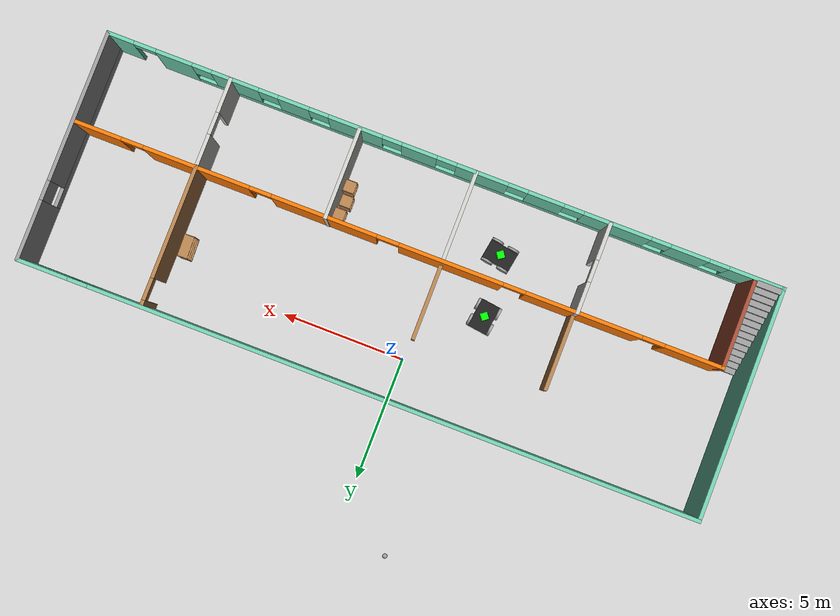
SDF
<sdf version="1.6">
 <world name="default">
  <plugin name="hello" filename="libhello.so"/>
  <light name="sun" type="directional">
   <pose>0 0 10 0 -0 0</pose>
   <diffuse>0.8 0.8 0.8 1</diffuse>
   <specular>0.2 0.2 0.2 1</specular>
   <attenuation>
    <range>1000</range>
    <constant>0.9</constant>
    <linear>0.01</linear>
    <quadratic>0.001</quadratic>
   </attenuation>
   <direction>-0.5 0.1 -0.9</direction>
  </light>
  <model name="ground_plane">
   <static>1</static>
   <link name="link">
    <collision name="collision">
     <geometry><plane><normal>0 0 1</normal><size>100 100</size></plane></geometry>
     <surface>
      <contact><collide_bitmask>65535</collide_bitmask></contact>
      <friction><ode><mu>100</mu><mu2>50</mu2></ode></friction>
     </surface>
    </collision>
    <visual name="visual">
     <cast_shadows>0</cast_shadows>
     <geometry><plane><normal>0 0 1</normal><size>100 100</size></plane></geometry>
     <material>
      <script><uri>file://media/materials/scripts/gazebo.material</uri><name>Gazebo/Grey</name></script>
     </material>
    </visual>
   </link>
  </model>
  <gravity>0 0 -9.8</gravity>
  <magnetic_field>6e-06 2.3e-05 -4.2e-05</magnetic_field>
  <atmosphere type="adiabatic"/>
  <physics name="default_physics" default="0" type="ode">
   <max_step_size>0.001</max_step_size>
   <real_time_factor>1</real_time_factor>
   <real_time_update_rate>1000</real_time_update_rate>
  </physics>
  <scene><ambient>0.4 0.4 0.4 1</ambient><background>0.7 0.7 0.7 1</background><shadows>1</shadows></scene>
  <spherical_coordinates>
   <surface_model>EARTH_WGS84</surface_model>
   <latitude_deg>0</latitude_deg>
   <longitude_deg>0</longitude_deg>
   <elevation>0</elevation>
   <heading_deg>0</heading_deg>
  </spherical_coordinates>
  <model name="4WheeledRobot">
   <link name="link_0">
    <pose>-0 -0 -0.041667 0 -0 0</pose>
    <inertial>
     <mass>1</mass>
     <inertia>
      <ixx>0.166667</ixx>
      <ixy>0</ixy>
      <ixz>0</ixz>
      <iyy>0.166667</iyy>
      <iyz>0</iyz>
      <izz>0.166667</izz>
     </inertia>
    </inertial>
    <visual name="visual">
     <geometry><box><size>1.2 0.8 0.2</size></box></geometry>
     <material>
      <lighting>1</lighting>
      <script><uri>file://media/materials/scripts/gazebo.material</uri><name>Gazebo/Black</name></script>
      <shader type="pixel"><normal_map>__default__</normal_map></shader>
      <ambient>1 0.1 0.1 1</ambient>
      <diffuse>0.7 0.7 0.7 1</diffuse>
      <specular>0.01 0.01 0.01 1</specular>
      <emissive>0 0 0 1</emissive>
     </material>
    </visual>
    <collision name="collision">
     <geometry><box><size>1.2 0.8 0.2</size></box></geometry>
     <surface>
      <friction>
       <ode><mu>1</mu><mu2>1</mu2><fdir1>0 0 0</fdir1><slip1>0</slip1><slip2>0</slip2></ode>
       <torsional>
        <coefficient>1</coefficient>
        <patch_radius>0</patch_radius>
        <surface_radius>0</surface_radius>
        <use_patch_radius>1</use_patch_radius>
        <ode><slip>0</slip></ode>
       </torsional>
      </friction>
      <bounce><restitution_coefficient>0</restitution_coefficient><threshold>1e+06</threshold></bounce>
      <contact>
       <collide_without_contact>0</collide_without_contact>
       <collide_without_contact_bitmask>1</collide_without_contact_bitmask>
       <collide_bitmask>1</collide_bitmask>
       <ode>
        <soft_cfm>0</soft_cfm>
        <soft_erp>0.2</soft_erp>
        <kp>1e+13</kp>
        <kd>1</kd>
        <max_vel>0.01</max_vel>
        <min_depth>0</min_depth>
       </ode>
       <bullet>
        <split_impulse>1</split_impulse>
        <split_impulse_penetration_threshold>-0.01</split_impulse_penetration_threshold>
        <soft_cfm>0</soft_cfm>
        <soft_erp>0.2</soft_erp>
        <kp>1e+13</kp>
        <kd>1</kd>
       </bullet>
      </contact>
     </surface>
    </collision>
   </link>
   <link name="link_1_clone_0">
    <pose>-0.35 0.450001 -0.041667 1.5708 -0 0</pose>
    <inertial>
     <mass>1</mass>
     <inertia><ixx>0.145833</ixx><ixy>0</ixy><ixz>0</ixz><iyy>0.145833</iyy><iyz>0</iyz><izz>0.125</izz></inertia>
    </inertial>
    <visual name="visual">
     <geometry><cylinder><radius>0.25</radius><length>0.1</length></cylinder></geometry>
     <material>
      <lighting>1</lighting>
      <script><uri>file://media/materials/scripts/gazebo.material</uri><name>Gazebo/Grey</name></script>
      <shader type="pixel"><normal_map>__default__</normal_map></shader>
      <ambient>1 1 1 0</ambient>
      <diffuse>0.7 0.7 0.7 1</diffuse>
      <specular>0.01 0.01 0.01 1</specular>
      <emissive>0 0 0 1</emissive>
     </material>
    </visual>
    <collision name="collision">
     <geometry><cylinder><radius>0.25</radius><length>0.1</length></cylinder></geometry>
     <surface>
      <friction>
       <ode><mu>1</mu><mu2>1</mu2><fdir1>0 0 0</fdir1><slip1>0</slip1><slip2>0</slip2></ode>
       <torsional>
        <coefficient>1</coefficient>
        <patch_radius>0</patch_radius>
        <surface_radius>0</surface_radius>
        <use_patch_radius>1</use_patch_radius>
        <ode><slip>0</slip></ode>
       </torsional>
      </friction>
      <bounce><restitution_coefficient>0</restitution_coefficient><threshold>1e+06</threshold></bounce>
      <contact>
       <collide_without_contact>0</collide_without_contact>
       <collide_without_contact_bitmask>1</collide_without_contact_bitmask>
       <collide_bitmask>1</collide_bitmask>
       <ode>
        <soft_cfm>0</soft_cfm>
        <soft_erp>0.2</soft_erp>
        <kp>1e+13</kp>
        <kd>1</kd>
        <max_vel>0.01</max_vel>
        <min_depth>0</min_depth>
       </ode>
       <bullet>
        <split_impulse>1</split_impulse>
        <split_impulse_penetration_threshold>-0.01</split_impulse_penetration_threshold>
        <soft_cfm>0</soft_cfm>
        <soft_erp>0.2</soft_erp>
        <kp>1e+13</kp>
        <kd>1</kd>
       </bullet>
      </contact>
     </surface>
    </collision>
   </link>
   <link name="link_1_clone_0_clone">
    <pose>-0.35 -0.450001 -0.041667 1.5708 -0 0</pose>
    <inertial>
     <mass>1</mass>
     <inertia><ixx>0.145833</ixx><ixy>0</ixy><ixz>0</ixz><iyy>0.145833</iyy><iyz>0</iyz><izz>0.125</izz></inertia>
    </inertial>
    <visual name="visual">
     <geometry><cylinder><radius>0.25</radius><length>0.1</length></cylinder></geometry>
     <material>
      <lighting>1</lighting>
      <script><uri>file://media/materials/scripts/gazebo.material</uri><name>Gazebo/Grey</name></script>
      <shader type="pixel"><normal_map>__default__</normal_map></shader>
      <ambient>1 1 1 0</ambient>
      <diffuse>0.7 0.7 0.7 1</diffuse>
      <specular>0.01 0.01 0.01 1</specular>
      <emissive>0 0 0 1</emissive>
     </material>
    </visual>
    <collision name="collision">
     <geometry><cylinder><radius>0.25</radius><length>0.1</length></cylinder></geometry>
     <surface>
      <friction>
       <ode><mu>1</mu><mu2>1</mu2><fdir1>0 0 0</fdir1><slip1>0</slip1><slip2>0</slip2></ode>
       <torsional>
        <coefficient>1</coefficient>
        <patch_radius>0</patch_radius>
        <surface_radius>0</surface_radius>
        <use_patch_radius>1</use_patch_radius>
        <ode><slip>0</slip></ode>
       </torsional>
      </friction>
      <bounce><restitution_coefficient>0</restitution_coefficient><threshold>1e+06</threshold></bounce>
      <contact>
       <collide_without_contact>0</collide_without_contact>
       <collide_without_contact_bitmask>1</collide_without_contact_bitmask>
       <collide_bitmask>1</collide_bitmask>
       <ode>
        <soft_cfm>0</soft_cfm>
        <soft_erp>0.2</soft_erp>
        <kp>1e+13</kp>
        <kd>1</kd>
        <max_vel>0.01</max_vel>
        <min_depth>0</min_depth>
       </ode>
       <bullet>
        <split_impulse>1</split_impulse>
        <split_impulse_penetration_threshold>-0.01</split_impulse_penetration_threshold>
        <soft_cfm>0</soft_cfm>
        <soft_erp>0.2</soft_erp>
        <kp>1e+13</kp>
        <kd>1</kd>
       </bullet>
      </contact>
     </surface>
    </collision>
   </link>
   <link name="link_1_clone_0_clone_0">
    <pose>0.35 -0.450001 -0.041667 1.5708 -0 0</pose>
    <inertial>
     <mass>1</mass>
     <inertia><ixx>0.145833</ixx><ixy>0</ixy><ixz>0</ixz><iyy>0.145833</iyy><iyz>0</iyz><izz>0.125</izz></inertia>
    </inertial>
    <visual name="visual">
     <geometry><cylinder><radius>0.25</radius><length>0.1</length></cylinder></geometry>
     <material>
      <lighting>1</lighting>
      <script><uri>file://media/materials/scripts/gazebo.material</uri><name>Gazebo/Grey</name></script>
      <shader type="pixel"><normal_map>__default__</normal_map></shader>
      <ambient>1 1 1 0</ambient>
      <diffuse>0.7 0.7 0.7 1</diffuse>
      <specular>0.01 0.01 0.01 1</specular>
      <emissive>0 0 0 1</emissive>
     </material>
    </visual>
    <collision name="collision">
     <geometry><cylinder><radius>0.25</radius><length>0.1</length></cylinder></geometry>
     <surface>
      <friction>
       <ode><mu>1</mu><mu2>1</mu2><fdir1>0 0 0</fdir1><slip1>0</slip1><slip2>0</slip2></ode>
       <torsional>
        <coefficient>1</coefficient>
        <patch_radius>0</patch_radius>
        <surface_radius>0</surface_radius>
        <use_patch_radius>1</use_patch_radius>
        <ode><slip>0</slip></ode>
       </torsional>
      </friction>
      <bounce><restitution_coefficient>0</restitution_coefficient><threshold>1e+06</threshold></bounce>
      <contact>
       <collide_without_contact>0</collide_without_contact>
       <collide_without_contact_bitmask>1</collide_without_contact_bitmask>
       <collide_bitmask>1</collide_bitmask>
       <ode>
        <soft_cfm>0</soft_cfm>
        <soft_erp>0.2</soft_erp>
        <kp>1e+13</kp>
        <kd>1</kd>
        <max_vel>0.01</max_vel>
        <min_depth>0</min_depth>
       </ode>
       <bullet>
        <split_impulse>1</split_impulse>
        <split_impulse_penetration_threshold>-0.01</split_impulse_penetration_threshold>
        <soft_cfm>0</soft_cfm>
        <soft_erp>0.2</soft_erp>
        <kp>1e+13</kp>
        <kd>1</kd>
       </bullet>
      </contact>
     </surface>
    </collision>
   </link>
   <link name="link_1_clone_1">
    <pose>0.35 0.450001 -0.041667 1.5708 -0 0</pose>
    <inertial>
     <mass>1</mass>
     <inertia><ixx>0.145833</ixx><ixy>0</ixy><ixz>0</ixz><iyy>0.145833</iyy><iyz>0</iyz><izz>0.125</izz></inertia>
    </inertial>
    <visual name="visual">
     <geometry><cylinder><radius>0.25</radius><length>0.1</length></cylinder></geometry>
     <material>
      <lighting>1</lighting>
      <script><uri>file://media/materials/scripts/gazebo.material</uri><name>Gazebo/Grey</name></script>
      <shader type="pixel"><normal_map>__default__</normal_map></shader>
      <ambient>1 1 1 0</ambient>
      <diffuse>0.7 0.7 0.7 1</diffuse>
      <specular>0.01 0.01 0.01 1</specular>
      <emissive>0 0 0 1</emissive>
     </material>
    </visual>
    <collision name="collision">
     <geometry><cylinder><radius>0.25</radius><length>0.1</length></cylinder></geometry>
     <surface>
      <friction>
       <ode><mu>1</mu><mu2>1</mu2><fdir1>0 0 0</fdir1><slip1>0</slip1><slip2>0</slip2></ode>
       <torsional>
        <coefficient>1</coefficient>
        <patch_radius>0</patch_radius>
        <surface_radius>0</surface_radius>
        <use_patch_radius>1</use_patch_radius>
        <ode><slip>0</slip></ode>
       </torsional>
      </friction>
      <bounce><restitution_coefficient>0</restitution_coefficient><threshold>1e+06</threshold></bounce>
      <contact>
       <collide_without_contact>0</collide_without_contact>
       <collide_without_contact_bitmask>1</collide_without_contact_bitmask>
       <collide_bitmask>1</collide_bitmask>
       <ode>
        <soft_cfm>0</soft_cfm>
        <soft_erp>0.2</soft_erp>
        <kp>1e+13</kp>
        <kd>1</kd>
        <max_vel>0.01</max_vel>
        <min_depth>0</min_depth>
       </ode>
       <bullet>
        <split_impulse>1</split_impulse>
        <split_impulse_penetration_threshold>-0.01</split_impulse_penetration_threshold>
        <soft_cfm>0</soft_cfm>
        <soft_erp>0.2</soft_erp>
        <kp>1e+13</kp>
        <kd>1</kd>
       </bullet>
      </contact>
     </surface>
    </collision>
   </link>
   <link name="link_2">
    <pose>-0 -0 0.208333 0 -0 0.7854</pose>
    <inertial>
     <mass>1</mass>
     <inertia>
      <ixx>0.166667</ixx>
      <ixy>0</ixy>
      <ixz>0</ixz>
      <iyy>0.166667</iyy>
      <iyz>0</iyz>
      <izz>0.166667</izz>
     </inertia>
    </inertial>
    <visual name="visual">
     <geometry><box><size>0.3 0.3 0.3</size></box></geometry>
     <material>
      <lighting>1</lighting>
      <script><uri>file://media/materials/scripts/gazebo.material</uri><name>Gazebo/Grey</name></script>
      <shader type="pixel"><normal_map>__default__</normal_map></shader>
      <ambient>0 1 0 1</ambient>
      <diffuse>0.7 0.7 0.7 1</diffuse>
      <specular>0.01 0.01 0.01 1</specular>
      <emissive>0 0 0 1</emissive>
     </material>
    </visual>
    <collision name="collision">
     <geometry><box><size>0.3 0.3 0.3</size></box></geometry>
     <surface>
      <friction>
       <ode><mu>1</mu><mu2>1</mu2><fdir1>0 0 0</fdir1><slip1>0</slip1><slip2>0</slip2></ode>
       <torsional>
        <coefficient>1</coefficient>
        <patch_radius>0</patch_radius>
        <surface_radius>0</surface_radius>
        <use_patch_radius>1</use_patch_radius>
        <ode><slip>0</slip></ode>
       </torsional>
      </friction>
      <bounce><restitution_coefficient>0</restitution_coefficient><threshold>1e+06</threshold></bounce>
      <contact>
       <collide_without_contact>0</collide_without_contact>
       <collide_without_contact_bitmask>1</collide_without_contact_bitmask>
       <collide_bitmask>1</collide_bitmask>
       <ode>
        <soft_cfm>0</soft_cfm>
        <soft_erp>0.2</soft_erp>
        <kp>1e+13</kp>
        <kd>1</kd>
        <max_vel>0.01</max_vel>
        <min_depth>0</min_depth>
       </ode>
       <bullet>
        <split_impulse>1</split_impulse>
        <split_impulse_penetration_threshold>-0.01</split_impulse_penetration_threshold>
        <soft_cfm>0</soft_cfm>
        <soft_erp>0.2</soft_erp>
        <kp>1e+13</kp>
        <kd>1</kd>
       </bullet>
      </contact>
     </surface>
    </collision>
   </link>
   <joint name="link_0_JOINT_3" type="revolute">
    <parent>link_0</parent>
    <child>link_1_clone_0_clone_0</child>
    <axis>
     <xyz>0 0 1</xyz>
     <use_parent_model_frame>0</use_parent_model_frame>
     <limit>
      <lower>-1.79769e+308</lower>
      <upper>1.79769e+308</upper>
      <effort>-1</effort>
      <velocity>-1</velocity>
     </limit>
     <dynamics>
      <spring_reference>0</spring_reference>
      <spring_stiffness>0</spring_stiffness>
      <damping>0</damping>
     </dynamics>
    </axis>
    <physics>
     <ode><limit><cfm>0</cfm><erp>0.2</erp></limit><suspension><cfm>0</cfm><erp>0.2</erp></suspension></ode>
    </physics>
   </joint>
   <joint name="link_0_JOINT_4" type="revolute">
    <parent>link_0</parent>
    <child>link_1_clone_0_clone</child>
    <axis>
     <xyz>0 0 1</xyz>
     <use_parent_model_frame>0</use_parent_model_frame>
     <limit>
      <lower>-1.79769e+308</lower>
      <upper>1.79769e+308</upper>
      <effort>-1</effort>
      <velocity>-1</velocity>
     </limit>
     <dynamics>
      <spring_reference>0</spring_reference>
      <spring_stiffness>0</spring_stiffness>
      <damping>0</damping>
     </dynamics>
    </axis>
    <physics>
     <ode><limit><cfm>0</cfm><erp>0.2</erp></limit><suspension><cfm>0</cfm><erp>0.2</erp></suspension></ode>
    </physics>
   </joint>
   <joint name="link_0_JOINT_5" type="revolute">
    <parent>link_0</parent>
    <child>link_1_clone_0</child>
    <axis>
     <xyz>0 0 1</xyz>
     <use_parent_model_frame>0</use_parent_model_frame>
     <limit>
      <lower>-1.79769e+308</lower>
      <upper>1.79769e+308</upper>
      <effort>-1</effort>
      <velocity>-1</velocity>
     </limit>
     <dynamics>
      <spring_reference>0</spring_reference>
      <spring_stiffness>0</spring_stiffness>
      <damping>0</damping>
     </dynamics>
    </axis>
    <physics>
     <ode><limit><cfm>0</cfm><erp>0.2</erp></limit><suspension><cfm>0</cfm><erp>0.2</erp></suspension></ode>
    </physics>
   </joint>
   <joint name="link_0_JOINT_6" type="revolute">
    <parent>link_0</parent>
    <child>link_1_clone_1</child>
    <axis>
     <xyz>0 0 1</xyz>
     <use_parent_model_frame>0</use_parent_model_frame>
     <limit>
      <lower>-1.79769e+308</lower>
      <upper>1.79769e+308</upper>
      <effort>-1</effort>
      <velocity>-1</velocity>
     </limit>
     <dynamics>
      <spring_reference>0</spring_reference>
      <spring_stiffness>0</spring_stiffness>
      <damping>0</damping>
     </dynamics>
    </axis>
    <physics>
     <ode><limit><cfm>0</cfm><erp>0.2</erp></limit><suspension><cfm>0</cfm><erp>0.2</erp></suspension></ode>
    </physics>
   </joint>
   <joint name="link_0_JOINT_7" type="fixed">
    <parent>link_0</parent>
    <child>link_2</child>
    <physics>
     <ode><limit><cfm>0</cfm><erp>0.2</erp></limit><suspension><cfm>0</cfm><erp>0.2</erp></suspension></ode>
    </physics>
   </joint>
   <static>0</static>
   <pose>-2.16795 -5.23865 0.291667 0 0 -0.166151</pose>
  </model>
  <model name="cabinet">
   <static>1</static>
   <link name="cabinet_bottom_plate">
    <inertial>
     <pose>0 0 -1 0 -0 0</pose>
     <inertia><ixx>2.05</ixx><ixy>0</ixy><ixz>0</ixz><iyy>2.05</iyy><iyz>0</iyz><izz>2.05</izz></inertia>
     <mass>25</mass>
    </inertial>
    <collision name="cabinet_bottom_plate_geom">
     <pose>0 0 0.01 0 -0 0</pose>
     <geometry><box><size>0.45 0.45 0.02</size></box></geometry>
    </collision>
    <visual name="cabinet_bottom_plate_geom_visual">
     <pose>0 0 0.01 0 -0 0</pose>
     <geometry><box><size>0.45 0.45 0.02</size></box></geometry>
     <material>
      <script><uri>file://media/materials/scripts/gazebo.material</uri><name>Gazebo/Wood</name></script>
     </material>
    </visual>
    <collision name="cabinet_bottom_plate_geom_cabinet_back_plate">
     <pose>0.235 0 0.51 0 -0 0</pose>
     <geometry><box><size>0.02 0.45 1.02</size></box></geometry>
    </collision>
    <visual name="cabinet_bottom_plate_geom_cabinet_back_plate_visual">
     <pose>0.235 0 0.51 0 -0 0</pose>
     <geometry><box><size>0.02 0.45 1.02</size></box></geometry>
     <material>
      <script><uri>file://media/materials/scripts/gazebo.material</uri><name>Gazebo/Wood</name></script>
     </material>
    </visual>
    <collision name="cabinet_bottom_plate_geom_cabinet_left_plate">
     <pose>0 0.235 0.51 0 -0 0</pose>
     <geometry><box><size>0.45 0.02 1.02</size></box></geometry>
    </collision>
    <visual name="cabinet_bottom_plate_geom_cabinet_left_plate_visual">
     <pose>0 0.235 0.51 0 -0 0</pose>
     <geometry><box><size>0.45 0.02 1.02</size></box></geometry>
     <material>
      <script><uri>file://media/materials/scripts/gazebo.material</uri><name>Gazebo/Wood</name></script>
     </material>
    </visual>
    <collision name="cabinet_bottom_plate_geom_cabinet_middle_plate">
     <pose>0 0 0.51 0 -0 0</pose>
     <geometry><box><size>0.45 0.45 0.02</size></box></geometry>
    </collision>
    <visual name="cabinet_bottom_plate_geom_cabinet_middle_plate_visual">
     <pose>0 0 0.51 0 -0 0</pose>
     <geometry><box><size>0.45 0.45 0.02</size></box></geometry>
     <material>
      <script><uri>file://media/materials/scripts/gazebo.material</uri><name>Gazebo/Wood</name></script>
     </material>
    </visual>
    <collision name="cabinet_bottom_plate_geom_cabinet_right_plate">
     <pose>0 -0.235 0.51 0 -0 0</pose>
     <geometry><box><size>0.45 0.02 1.02</size></box></geometry>
    </collision>
    <visual name="cabinet_bottom_plate_geom_cabinet_right_plate_visual">
     <pose>0 -0.235 0.51 0 -0 0</pose>
     <geometry><box><size>0.45 0.02 1.02</size></box></geometry>
     <material>
      <script><uri>file://media/materials/scripts/gazebo.material</uri><name>Gazebo/Wood</name></script>
     </material>
    </visual>
    <collision name="cabinet_bottom_plate_geom_cabinet_top_plate">
     <pose>0 0 1.01 0 -0 0</pose>
     <geometry><box><size>0.45 0.45 0.02</size></box></geometry>
    </collision>
    <visual name="cabinet_bottom_plate_geom_cabinet_top_plate_visual">
     <pose>0 0 1.01 0 -0 0</pose>
     <geometry><box><size>0.45 0.45 0.02</size></box></geometry>
     <material>
      <script><uri>file://media/materials/scripts/gazebo.material</uri><name>Gazebo/Wood</name></script>
     </material>
    </visual>
   </link>
   <pose>4.32812 -5.59314 0 0 -0 0</pose>
  </model>
  <model name="cabinet_0">
   <static>1</static>
   <link name="cabinet_bottom_plate">
    <inertial>
     <pose>0 0 -1 0 -0 0</pose>
     <inertia><ixx>2.05</ixx><ixy>0</ixy><ixz>0</ixz><iyy>2.05</iyy><iyz>0</iyz><izz>2.05</izz></inertia>
     <mass>25</mass>
    </inertial>
    <collision name="cabinet_bottom_plate_geom">
     <pose>0 0 0.01 0 -0 0</pose>
     <geometry><box><size>0.45 0.45 0.02</size></box></geometry>
    </collision>
    <visual name="cabinet_bottom_plate_geom_visual">
     <pose>0 0 0.01 0 -0 0</pose>
     <geometry><box><size>0.45 0.45 0.02</size></box></geometry>
     <material>
      <script><uri>file://media/materials/scripts/gazebo.material</uri><name>Gazebo/Wood</name></script>
     </material>
    </visual>
    <collision name="cabinet_bottom_plate_geom_cabinet_back_plate">
     <pose>0.235 0 0.51 0 -0 0</pose>
     <geometry><box><size>0.02 0.45 1.02</size></box></geometry>
    </collision>
    <visual name="cabinet_bottom_plate_geom_cabinet_back_plate_visual">
     <pose>0.235 0 0.51 0 -0 0</pose>
     <geometry><box><size>0.02 0.45 1.02</size></box></geometry>
     <material>
      <script><uri>file://media/materials/scripts/gazebo.material</uri><name>Gazebo/Wood</name></script>
     </material>
    </visual>
    <collision name="cabinet_bottom_plate_geom_cabinet_left_plate">
     <pose>0 0.235 0.51 0 -0 0</pose>
     <geometry><box><size>0.45 0.02 1.02</size></box></geometry>
    </collision>
    <visual name="cabinet_bottom_plate_geom_cabinet_left_plate_visual">
     <pose>0 0.235 0.51 0 -0 0</pose>
     <geometry><box><size>0.45 0.02 1.02</size></box></geometry>
     <material>
      <script><uri>file://media/materials/scripts/gazebo.material</uri><name>Gazebo/Wood</name></script>
     </material>
    </visual>
    <collision name="cabinet_bottom_plate_geom_cabinet_middle_plate">
     <pose>0 0 0.51 0 -0 0</pose>
     <geometry><box><size>0.45 0.45 0.02</size></box></geometry>
    </collision>
    <visual name="cabinet_bottom_plate_geom_cabinet_middle_plate_visual">
     <pose>0 0 0.51 0 -0 0</pose>
     <geometry><box><size>0.45 0.45 0.02</size></box></geometry>
     <material>
      <script><uri>file://media/materials/scripts/gazebo.material</uri><name>Gazebo/Wood</name></script>
     </material>
    </visual>
    <collision name="cabinet_bottom_plate_geom_cabinet_right_plate">
     <pose>0 -0.235 0.51 0 -0 0</pose>
     <geometry><box><size>0.45 0.02 1.02</size></box></geometry>
    </collision>
    <visual name="cabinet_bottom_plate_geom_cabinet_right_plate_visual">
     <pose>0 -0.235 0.51 0 -0 0</pose>
     <geometry><box><size>0.45 0.02 1.02</size></box></geometry>
     <material>
      <script><uri>file://media/materials/scripts/gazebo.material</uri><name>Gazebo/Wood</name></script>
     </material>
    </visual>
    <collision name="cabinet_bottom_plate_geom_cabinet_top_plate">
     <pose>0 0 1.01 0 -0 0</pose>
     <geometry><box><size>0.45 0.45 0.02</size></box></geometry>
    </collision>
    <visual name="cabinet_bottom_plate_geom_cabinet_top_plate_visual">
     <pose>0 0 1.01 0 -0 0</pose>
     <geometry><box><size>0.45 0.45 0.02</size></box></geometry>
     <material>
      <script><uri>file://media/materials/scripts/gazebo.material</uri><name>Gazebo/Wood</name></script>
     </material>
    </visual>
   </link>
   <pose>4.25631 -5.00246 0 0 -0 0</pose>
  </model>
  <model name="cabinet_1">
   <static>1</static>
   <link name="cabinet_bottom_plate">
    <inertial>
     <pose>0 0 -1 0 -0 0</pose>
     <inertia><ixx>2.05</ixx><ixy>0</ixy><ixz>0</ixz><iyy>2.05</iyy><iyz>0</iyz><izz>2.05</izz></inertia>
     <mass>25</mass>
    </inertial>
    <collision name="cabinet_bottom_plate_geom">
     <pose>0 0 0.01 0 -0 0</pose>
     <geometry><box><size>0.45 0.45 0.02</size></box></geometry>
    </collision>
    <visual name="cabinet_bottom_plate_geom_visual">
     <pose>0 0 0.01 0 -0 0</pose>
     <geometry><box><size>0.45 0.45 0.02</size></box></geometry>
     <material>
      <script><uri>file://media/materials/scripts/gazebo.material</uri><name>Gazebo/Wood</name></script>
     </material>
    </visual>
    <collision name="cabinet_bottom_plate_geom_cabinet_back_plate">
     <pose>0.235 0 0.51 0 -0 0</pose>
     <geometry><box><size>0.02 0.45 1.02</size></box></geometry>
    </collision>
    <visual name="cabinet_bottom_plate_geom_cabinet_back_plate_visual">
     <pose>0.235 0 0.51 0 -0 0</pose>
     <geometry><box><size>0.02 0.45 1.02</size></box></geometry>
     <material>
      <script><uri>file://media/materials/scripts/gazebo.material</uri><name>Gazebo/Wood</name></script>
     </material>
    </visual>
    <collision name="cabinet_bottom_plate_geom_cabinet_left_plate">
     <pose>0 0.235 0.51 0 -0 0</pose>
     <geometry><box><size>0.45 0.02 1.02</size></box></geometry>
    </collision>
    <visual name="cabinet_bottom_plate_geom_cabinet_left_plate_visual">
     <pose>0 0.235 0.51 0 -0 0</pose>
     <geometry><box><size>0.45 0.02 1.02</size></box></geometry>
     <material>
      <script><uri>file://media/materials/scripts/gazebo.material</uri><name>Gazebo/Wood</name></script>
     </material>
    </visual>
    <collision name="cabinet_bottom_plate_geom_cabinet_middle_plate">
     <pose>0 0 0.51 0 -0 0</pose>
     <geometry><box><size>0.45 0.45 0.02</size></box></geometry>
    </collision>
    <visual name="cabinet_bottom_plate_geom_cabinet_middle_plate_visual">
     <pose>0 0 0.51 0 -0 0</pose>
     <geometry><box><size>0.45 0.45 0.02</size></box></geometry>
     <material>
      <script><uri>file://media/materials/scripts/gazebo.material</uri><name>Gazebo/Wood</name></script>
     </material>
    </visual>
    <collision name="cabinet_bottom_plate_geom_cabinet_right_plate">
     <pose>0 -0.235 0.51 0 -0 0</pose>
     <geometry><box><size>0.45 0.02 1.02</size></box></geometry>
    </collision>
    <visual name="cabinet_bottom_plate_geom_cabinet_right_plate_visual">
     <pose>0 -0.235 0.51 0 -0 0</pose>
     <geometry><box><size>0.45 0.02 1.02</size></box></geometry>
     <material>
      <script><uri>file://media/materials/scripts/gazebo.material</uri><name>Gazebo/Wood</name></script>
     </material>
    </visual>
    <collision name="cabinet_bottom_plate_geom_cabinet_top_plate">
     <pose>0 0 1.01 0 -0 0</pose>
     <geometry><box><size>0.45 0.45 0.02</size></box></geometry>
    </collision>
    <visual name="cabinet_bottom_plate_geom_cabinet_top_plate_visual">
     <pose>0 0 1.01 0 -0 0</pose>
     <geometry><box><size>0.45 0.45 0.02</size></box></geometry>
     <material>
      <script><uri>file://media/materials/scripts/gazebo.material</uri><name>Gazebo/Wood</name></script>
     </material>
    </visual>
   </link>
   <pose>4.33213 -4.41527 0 0 -0 0</pose>
  </model>
  <model name="bookshelf">
   <static>1</static>
   <link name="link">
    <inertial><mass>1</mass></inertial>
    <collision name="back">
     <pose>0 0.005 0.6 0 -0 0</pose>
     <geometry><box><size>0.9 0.01 1.2</size></box></geometry>
    </collision>
    <visual name="visual1">
     <pose>0 0.005 0.6 0 -0 0</pose>
     <geometry><box><size>0.9 0.01 1.2</size></box></geometry>
     <material>
      <script><uri>file://media/materials/scripts/gazebo.material</uri><name>Gazebo/Wood</name></script>
     </material>
    </visual>
    <collision name="left_side">
     <pose>0.45 -0.195 0.6 0 -0 0</pose>
     <geometry><box><size>0.02 0.4 1.2</size></box></geometry>
    </collision>
    <visual name="visual2">
     <pose>0.45 -0.195 0.6 0 -0 0</pose>
     <geometry><box><size>0.02 0.4 1.2</size></box></geometry>
     <material>
      <script><uri>file://media/materials/scripts/gazebo.material</uri><name>Gazebo/Wood</name></script>
     </material>
    </visual>
    <collision name="right_side">
     <pose>-0.45 -0.195 0.6 0 -0 0</pose>
     <geometry><box><size>0.02 0.4 1.2</size></box></geometry>
    </collision>
    <visual name="visual3">
     <pose>-0.45 -0.195 0.6 0 -0 0</pose>
     <geometry><box><size>0.02 0.4 1.2</size></box></geometry>
     <material>
      <script><uri>file://media/materials/scripts/gazebo.material</uri><name>Gazebo/Wood</name></script>
     </material>
    </visual>
    <collision name="bottom">
     <pose>0 -0.195 0.03 0 -0 0</pose>
     <geometry><box><size>0.88 0.4 0.06</size></box></geometry>
    </collision>
    <visual name="visual4">
     <pose>0 -0.195 0.03 0 -0 0</pose>
     <geometry><box><size>0.88 0.4 0.06</size></box></geometry>
     <material>
      <script><uri>file://media/materials/scripts/gazebo.material</uri><name>Gazebo/Wood</name></script>
     </material>
    </visual>
    <collision name="top">
     <pose>0 -0.195 1.19 0 -0 0</pose>
     <geometry><box><size>0.88 0.4 0.02</size></box></geometry>
    </collision>
    <visual name="visual5">
     <pose>0 -0.195 1.19 0 -0 0</pose>
     <geometry><box><size>0.88 0.4 0.02</size></box></geometry>
     <material>
      <script><uri>file://media/materials/scripts/gazebo.material</uri><name>Gazebo/Wood</name></script>
     </material>
    </visual>
    <collision name="low_shelf">
     <pose>0 -0.195 0.43 0 -0 0</pose>
     <geometry><box><size>0.88 0.4 0.02</size></box></geometry>
    </collision>
    <visual name="visual6">
     <pose>0 -0.195 0.43 0 -0 0</pose>
     <geometry><box><size>0.88 0.4 0.02</size></box></geometry>
     <material>
      <script><uri>file://media/materials/scripts/gazebo.material</uri><name>Gazebo/Wood</name></script>
     </material>
    </visual>
    <collision name="high_shelf">
     <pose>0 -0.195 0.8 0 -0 0</pose>
     <geometry><box><size>0.88 0.4 0.02</size></box></geometry>
    </collision>
    <visual name="visual7">
     <pose>0 -0.195 0.8 0 -0 0</pose>
     <geometry><box><size>0.88 0.4 0.02</size></box></geometry>
     <material>
      <script><uri>file://media/materials/scripts/gazebo.material</uri><name>Gazebo/Wood</name></script>
     </material>
    </visual>
   </link>
   <pose>9.64485 -1.08676 0 0 0 -1.5382</pose>
  </model>
  <model name="4WheeledRobot_clone">
   <link name="link_0">
    <pose>-0 -0 -0.041667 0 -0 0</pose>
    <inertial>
     <mass>1</mass>
     <inertia>
      <ixx>0.166667</ixx>
      <ixy>0</ixy>
      <ixz>0</ixz>
      <iyy>0.166667</iyy>
      <iyz>0</iyz>
      <izz>0.166667</izz>
     </inertia>
    </inertial>
    <visual name="visual">
     <geometry><box><size>1.2 0.8 0.2</size></box></geometry>
     <material>
      <lighting>1</lighting>
      <script><uri>file://media/materials/scripts/gazebo.material</uri><name>Gazebo/Black</name></script>
      <shader type="pixel"><normal_map>__default__</normal_map></shader>
      <ambient>1 0.1 0.1 1</ambient>
      <diffuse>0.7 0.7 0.7 1</diffuse>
      <specular>0.01 0.01 0.01 1</specular>
      <emissive>0 0 0 1</emissive>
     </material>
    </visual>
    <collision name="collision">
     <geometry><box><size>1.2 0.8 0.2</size></box></geometry>
     <surface>
      <friction>
       <ode><mu>1</mu><mu2>1</mu2><fdir1>0 0 0</fdir1><slip1>0</slip1><slip2>0</slip2></ode>
       <torsional>
        <coefficient>1</coefficient>
        <patch_radius>0</patch_radius>
        <surface_radius>0</surface_radius>
        <use_patch_radius>1</use_patch_radius>
        <ode><slip>0</slip></ode>
       </torsional>
      </friction>
      <bounce><restitution_coefficient>0</restitution_coefficient><threshold>1e+06</threshold></bounce>
      <contact>
       <collide_without_contact>0</collide_without_contact>
       <collide_without_contact_bitmask>1</collide_without_contact_bitmask>
       <collide_bitmask>1</collide_bitmask>
       <ode>
        <soft_cfm>0</soft_cfm>
        <soft_erp>0.2</soft_erp>
        <kp>1e+13</kp>
        <kd>1</kd>
        <max_vel>0.01</max_vel>
        <min_depth>0</min_depth>
       </ode>
       <bullet>
        <split_impulse>1</split_impulse>
        <split_impulse_penetration_threshold>-0.01</split_impulse_penetration_threshold>
        <soft_cfm>0</soft_cfm>
        <soft_erp>0.2</soft_erp>
        <kp>1e+13</kp>
        <kd>1</kd>
       </bullet>
      </contact>
     </surface>
    </collision>
   </link>
   <link name="link_1_clone_0">
    <pose>-0.35 0.450001 -0.041667 1.5708 -0 0</pose>
    <inertial>
     <mass>1</mass>
     <inertia><ixx>0.145833</ixx><ixy>0</ixy><ixz>0</ixz><iyy>0.145833</iyy><iyz>0</iyz><izz>0.125</izz></inertia>
    </inertial>
    <visual name="visual">
     <geometry><cylinder><radius>0.25</radius><length>0.1</length></cylinder></geometry>
     <material>
      <lighting>1</lighting>
      <script><uri>file://media/materials/scripts/gazebo.material</uri><name>Gazebo/Grey</name></script>
      <shader type="pixel"><normal_map>__default__</normal_map></shader>
      <ambient>1 1 1 0</ambient>
      <diffuse>0.7 0.7 0.7 1</diffuse>
      <specular>0.01 0.01 0.01 1</specular>
      <emissive>0 0 0 1</emissive>
     </material>
    </visual>
    <collision name="collision">
     <geometry><cylinder><radius>0.25</radius><length>0.1</length></cylinder></geometry>
     <surface>
      <friction>
       <ode><mu>1</mu><mu2>1</mu2><fdir1>0 0 0</fdir1><slip1>0</slip1><slip2>0</slip2></ode>
       <torsional>
        <coefficient>1</coefficient>
        <patch_radius>0</patch_radius>
        <surface_radius>0</surface_radius>
        <use_patch_radius>1</use_patch_radius>
        <ode><slip>0</slip></ode>
       </torsional>
      </friction>
      <bounce><restitution_coefficient>0</restitution_coefficient><threshold>1e+06</threshold></bounce>
      <contact>
       <collide_without_contact>0</collide_without_contact>
       <collide_without_contact_bitmask>1</collide_without_contact_bitmask>
       <collide_bitmask>1</collide_bitmask>
       <ode>
        <soft_cfm>0</soft_cfm>
        <soft_erp>0.2</soft_erp>
        <kp>1e+13</kp>
        <kd>1</kd>
        <max_vel>0.01</max_vel>
        <min_depth>0</min_depth>
       </ode>
       <bullet>
        <split_impulse>1</split_impulse>
        <split_impulse_penetration_threshold>-0.01</split_impulse_penetration_threshold>
        <soft_cfm>0</soft_cfm>
        <soft_erp>0.2</soft_erp>
        <kp>1e+13</kp>
        <kd>1</kd>
       </bullet>
      </contact>
     </surface>
    </collision>
   </link>
   <link name="link_1_clone_0_clone">
    <pose>-0.35 -0.450001 -0.041667 1.5708 -0 0</pose>
    <inertial>
     <mass>1</mass>
     <inertia><ixx>0.145833</ixx><ixy>0</ixy><ixz>0</ixz><iyy>0.145833</iyy><iyz>0</iyz><izz>0.125</izz></inertia>
    </inertial>
    <visual name="visual">
     <geometry><cylinder><radius>0.25</radius><length>0.1</length></cylinder></geometry>
     <material>
      <lighting>1</lighting>
      <script><uri>file://media/materials/scripts/gazebo.material</uri><name>Gazebo/Grey</name></script>
      <shader type="pixel"><normal_map>__default__</normal_map></shader>
      <ambient>1 1 1 0</ambient>
      <diffuse>0.7 0.7 0.7 1</diffuse>
      <specular>0.01 0.01 0.01 1</specular>
      <emissive>0 0 0 1</emissive>
     </material>
    </visual>
    <collision name="collision">
     <geometry><cylinder><radius>0.25</radius><length>0.1</length></cylinder></geometry>
     <surface>
      <friction>
       <ode><mu>1</mu><mu2>1</mu2><fdir1>0 0 0</fdir1><slip1>0</slip1><slip2>0</slip2></ode>
       <torsional>
        <coefficient>1</coefficient>
        <patch_radius>0</patch_radius>
        <surface_radius>0</surface_radius>
        <use_patch_radius>1</use_patch_radius>
        <ode><slip>0</slip></ode>
       </torsional>
      </friction>
      <bounce><restitution_coefficient>0</restitution_coefficient><threshold>1e+06</threshold></bounce>
      <contact>
       <collide_without_contact>0</collide_without_contact>
       <collide_without_contact_bitmask>1</collide_without_contact_bitmask>
       <collide_bitmask>1</collide_bitmask>
       <ode>
        <soft_cfm>0</soft_cfm>
        <soft_erp>0.2</soft_erp>
        <kp>1e+13</kp>
        <kd>1</kd>
        <max_vel>0.01</max_vel>
        <min_depth>0</min_depth>
       </ode>
       <bullet>
        <split_impulse>1</split_impulse>
        <split_impulse_penetration_threshold>-0.01</split_impulse_penetration_threshold>
        <soft_cfm>0</soft_cfm>
        <soft_erp>0.2</soft_erp>
        <kp>1e+13</kp>
        <kd>1</kd>
       </bullet>
      </contact>
     </surface>
    </collision>
   </link>
   <link name="link_1_clone_0_clone_0">
    <pose>0.35 -0.450001 -0.041667 1.5708 -0 0</pose>
    <inertial>
     <mass>1</mass>
     <inertia><ixx>0.145833</ixx><ixy>0</ixy><ixz>0</ixz><iyy>0.145833</iyy><iyz>0</iyz><izz>0.125</izz></inertia>
    </inertial>
    <visual name="visual">
     <geometry><cylinder><radius>0.25</radius><length>0.1</length></cylinder></geometry>
     <material>
      <lighting>1</lighting>
      <script><uri>file://media/materials/scripts/gazebo.material</uri><name>Gazebo/Grey</name></script>
      <shader type="pixel"><normal_map>__default__</normal_map></shader>
      <ambient>1 1 1 0</ambient>
      <diffuse>0.7 0.7 0.7 1</diffuse>
      <specular>0.01 0.01 0.01 1</specular>
      <emissive>0 0 0 1</emissive>
     </material>
    </visual>
    <collision name="collision">
     <geometry><cylinder><radius>0.25</radius><length>0.1</length></cylinder></geometry>
     <surface>
      <friction>
       <ode><mu>1</mu><mu2>1</mu2><fdir1>0 0 0</fdir1><slip1>0</slip1><slip2>0</slip2></ode>
       <torsional>
        <coefficient>1</coefficient>
        <patch_radius>0</patch_radius>
        <surface_radius>0</surface_radius>
        <use_patch_radius>1</use_patch_radius>
        <ode><slip>0</slip></ode>
       </torsional>
      </friction>
      <bounce><restitution_coefficient>0</restitution_coefficient><threshold>1e+06</threshold></bounce>
      <contact>
       <collide_without_contact>0</collide_without_contact>
       <collide_without_contact_bitmask>1</collide_without_contact_bitmask>
       <collide_bitmask>1</collide_bitmask>
       <ode>
        <soft_cfm>0</soft_cfm>
        <soft_erp>0.2</soft_erp>
        <kp>1e+13</kp>
        <kd>1</kd>
        <max_vel>0.01</max_vel>
        <min_depth>0</min_depth>
       </ode>
       <bullet>
        <split_impulse>1</split_impulse>
        <split_impulse_penetration_threshold>-0.01</split_impulse_penetration_threshold>
        <soft_cfm>0</soft_cfm>
        <soft_erp>0.2</soft_erp>
        <kp>1e+13</kp>
        <kd>1</kd>
       </bullet>
      </contact>
     </surface>
    </collision>
   </link>
   <link name="link_1_clone_1">
    <pose>0.35 0.450001 -0.041667 1.5708 -0 0</pose>
    <inertial>
     <mass>1</mass>
     <inertia><ixx>0.145833</ixx><ixy>0</ixy><ixz>0</ixz><iyy>0.145833</iyy><iyz>0</iyz><izz>0.125</izz></inertia>
    </inertial>
    <visual name="visual">
     <geometry><cylinder><radius>0.25</radius><length>0.1</length></cylinder></geometry>
     <material>
      <lighting>1</lighting>
      <script><uri>file://media/materials/scripts/gazebo.material</uri><name>Gazebo/Grey</name></script>
      <shader type="pixel"><normal_map>__default__</normal_map></shader>
      <ambient>1 1 1 0</ambient>
      <diffuse>0.7 0.7 0.7 1</diffuse>
      <specular>0.01 0.01 0.01 1</specular>
      <emissive>0 0 0 1</emissive>
     </material>
    </visual>
    <collision name="collision">
     <geometry><cylinder><radius>0.25</radius><length>0.1</length></cylinder></geometry>
     <surface>
      <friction>
       <ode><mu>1</mu><mu2>1</mu2><fdir1>0 0 0</fdir1><slip1>0</slip1><slip2>0</slip2></ode>
       <torsional>
        <coefficient>1</coefficient>
        <patch_radius>0</patch_radius>
        <surface_radius>0</surface_radius>
        <use_patch_radius>1</use_patch_radius>
        <ode><slip>0</slip></ode>
       </torsional>
      </friction>
      <bounce><restitution_coefficient>0</restitution_coefficient><threshold>1e+06</threshold></bounce>
      <contact>
       <collide_without_contact>0</collide_without_contact>
       <collide_without_contact_bitmask>1</collide_without_contact_bitmask>
       <collide_bitmask>1</collide_bitmask>
       <ode>
        <soft_cfm>0</soft_cfm>
        <soft_erp>0.2</soft_erp>
        <kp>1e+13</kp>
        <kd>1</kd>
        <max_vel>0.01</max_vel>
        <min_depth>0</min_depth>
       </ode>
       <bullet>
        <split_impulse>1</split_impulse>
        <split_impulse_penetration_threshold>-0.01</split_impulse_penetration_threshold>
        <soft_cfm>0</soft_cfm>
        <soft_erp>0.2</soft_erp>
        <kp>1e+13</kp>
        <kd>1</kd>
       </bullet>
      </contact>
     </surface>
    </collision>
   </link>
   <link name="link_2">
    <pose>-0 -0 0.208333 0 -0 0.7854</pose>
    <inertial>
     <mass>1</mass>
     <inertia>
      <ixx>0.166667</ixx>
      <ixy>0</ixy>
      <ixz>0</ixz>
      <iyy>0.166667</iyy>
      <iyz>0</iyz>
      <izz>0.166667</izz>
     </inertia>
    </inertial>
    <visual name="visual">
     <geometry><box><size>0.3 0.3 0.3</size></box></geometry>
     <material>
      <lighting>1</lighting>
      <script><uri>file://media/materials/scripts/gazebo.material</uri><name>Gazebo/Grey</name></script>
      <shader type="pixel"><normal_map>__default__</normal_map></shader>
      <ambient>0 1 0 1</ambient>
      <diffuse>0.7 0.7 0.7 1</diffuse>
      <specular>0.01 0.01 0.01 1</specular>
      <emissive>0 0 0 1</emissive>
     </material>
    </visual>
    <collision name="collision">
     <geometry><box><size>0.3 0.3 0.3</size></box></geometry>
     <surface>
      <friction>
       <ode><mu>1</mu><mu2>1</mu2><fdir1>0 0 0</fdir1><slip1>0</slip1><slip2>0</slip2></ode>
       <torsional>
        <coefficient>1</coefficient>
        <patch_radius>0</patch_radius>
        <surface_radius>0</surface_radius>
        <use_patch_radius>1</use_patch_radius>
        <ode><slip>0</slip></ode>
       </torsional>
      </friction>
      <bounce><restitution_coefficient>0</restitution_coefficient><threshold>1e+06</threshold></bounce>
      <contact>
       <collide_without_contact>0</collide_without_contact>
       <collide_without_contact_bitmask>1</collide_without_contact_bitmask>
       <collide_bitmask>1</collide_bitmask>
       <ode>
        <soft_cfm>0</soft_cfm>
        <soft_erp>0.2</soft_erp>
        <kp>1e+13</kp>
        <kd>1</kd>
        <max_vel>0.01</max_vel>
        <min_depth>0</min_depth>
       </ode>
       <bullet>
        <split_impulse>1</split_impulse>
        <split_impulse_penetration_threshold>-0.01</split_impulse_penetration_threshold>
        <soft_cfm>0</soft_cfm>
        <soft_erp>0.2</soft_erp>
        <kp>1e+13</kp>
        <kd>1</kd>
       </bullet>
      </contact>
     </surface>
    </collision>
   </link>
   <joint name="link_0_JOINT_3" type="revolute">
    <parent>link_0</parent>
    <child>link_1_clone_0_clone_0</child>
    <axis>
     <xyz>0 0 1</xyz>
     <use_parent_model_frame>0</use_parent_model_frame>
     <limit>
      <lower>-1.79769e+308</lower>
      <upper>1.79769e+308</upper>
      <effort>-1</effort>
      <velocity>-1</velocity>
     </limit>
     <dynamics>
      <spring_reference>0</spring_reference>
      <spring_stiffness>0</spring_stiffness>
      <damping>0</damping>
     </dynamics>
    </axis>
    <physics>
     <ode><limit><cfm>0</cfm><erp>0.2</erp></limit><suspension><cfm>0</cfm><erp>0.2</erp></suspension></ode>
    </physics>
   </joint>
   <joint name="link_0_JOINT_4" type="revolute">
    <parent>link_0</parent>
    <child>link_1_clone_0_clone</child>
    <axis>
     <xyz>0 0 1</xyz>
     <use_parent_model_frame>0</use_parent_model_frame>
     <limit>
      <lower>-1.79769e+308</lower>
      <upper>1.79769e+308</upper>
      <effort>-1</effort>
      <velocity>-1</velocity>
     </limit>
     <dynamics>
      <spring_reference>0</spring_reference>
      <spring_stiffness>0</spring_stiffness>
      <damping>0</damping>
     </dynamics>
    </axis>
    <physics>
     <ode><limit><cfm>0</cfm><erp>0.2</erp></limit><suspension><cfm>0</cfm><erp>0.2</erp></suspension></ode>
    </physics>
   </joint>
   <joint name="link_0_JOINT_5" type="revolute">
    <parent>link_0</parent>
    <child>link_1_clone_0</child>
    <axis>
     <xyz>0 0 1</xyz>
     <use_parent_model_frame>0</use_parent_model_frame>
     <limit>
      <lower>-1.79769e+308</lower>
      <upper>1.79769e+308</upper>
      <effort>-1</effort>
      <velocity>-1</velocity>
     </limit>
     <dynamics>
      <spring_reference>0</spring_reference>
      <spring_stiffness>0</spring_stiffness>
      <damping>0</damping>
     </dynamics>
    </axis>
    <physics>
     <ode><limit><cfm>0</cfm><erp>0.2</erp></limit><suspension><cfm>0</cfm><erp>0.2</erp></suspension></ode>
    </physics>
   </joint>
   <joint name="link_0_JOINT_6" type="revolute">
    <parent>link_0</parent>
    <child>link_1_clone_1</child>
    <axis>
     <xyz>0 0 1</xyz>
     <use_parent_model_frame>0</use_parent_model_frame>
     <limit>
      <lower>-1.79769e+308</lower>
      <upper>1.79769e+308</upper>
      <effort>-1</effort>
      <velocity>-1</velocity>
     </limit>
     <dynamics>
      <spring_reference>0</spring_reference>
      <spring_stiffness>0</spring_stiffness>
      <damping>0</damping>
     </dynamics>
    </axis>
    <physics>
     <ode><limit><cfm>0</cfm><erp>0.2</erp></limit><suspension><cfm>0</cfm><erp>0.2</erp></suspension></ode>
    </physics>
   </joint>
   <joint name="link_0_JOINT_7" type="fixed">
    <parent>link_0</parent>
    <child>link_2</child>
    <physics>
     <ode><limit><cfm>0</cfm><erp>0.2</erp></limit><suspension><cfm>0</cfm><erp>0.2</erp></suspension></ode>
    </physics>
   </joint>
   <static>0</static>
   <pose>-2.43153 -2.73646 0.291666 -2e-06 -0 -1.70096</pose>
  </model>
  <model name="Room2">
   <pose>1.20997 -2.96921 0 0 -0 0</pose>
   <link name="Stairs_0">
    <visual name="Stairs_0_Visual_0">
     <pose>-13.2569 -1.25437 0.083333 0 -0 0</pose>
     <geometry><box><size>1 0.233333 0.166667</size></box></geometry>
     <material>
      <script><uri>file://media/materials/scripts/gazebo.material</uri><name>Gazebo/Grey</name></script>
      <ambient>1 1 1 1</ambient>
     </material>
     <meta><layer>0</layer></meta>
    </visual>
    <collision name="Stairs_0_Collision_0">
     <geometry><box><size>1 0.233333 0.166667</size></box></geometry>
     <pose>-13.2569 -1.25437 0.083333 0 -0 0</pose>
    </collision>
    <visual name="Stairs_0_Visual_1">
     <pose>-13.2569 -1.4877 0.25 0 -0 0</pose>
     <geometry><box><size>1 0.233333 0.166667</size></box></geometry>
     <material>
      <script><uri>file://media/materials/scripts/gazebo.material</uri><name>Gazebo/Grey</name></script>
      <ambient>1 1 1 1</ambient>
     </material>
     <meta><layer>0</layer></meta>
    </visual>
    <collision name="Stairs_0_Collision_1">
     <geometry><box><size>1 0.233333 0.166667</size></box></geometry>
     <pose>-13.2569 -1.4877 0.25 0 -0 0</pose>
    </collision>
    <visual name="Stairs_0_Visual_2">
     <pose>-13.2569 -1.72104 0.416667 0 -0 0</pose>
     <geometry><box><size>1 0.233333 0.166667</size></box></geometry>
     <material>
      <script><uri>file://media/materials/scripts/gazebo.material</uri><name>Gazebo/Grey</name></script>
      <ambient>1 1 1 1</ambient>
     </material>
     <meta><layer>0</layer></meta>
    </visual>
    <collision name="Stairs_0_Collision_2">
     <geometry><box><size>1 0.233333 0.166667</size></box></geometry>
     <pose>-13.2569 -1.72104 0.416667 0 -0 0</pose>
    </collision>
    <visual name="Stairs_0_Visual_3">
     <pose>-13.2569 -1.95437 0.583333 0 -0 0</pose>
     <geometry><box><size>1 0.233333 0.166667</size></box></geometry>
     <material>
      <script><uri>file://media/materials/scripts/gazebo.material</uri><name>Gazebo/Grey</name></script>
      <ambient>1 1 1 1</ambient>
     </material>
     <meta><layer>0</layer></meta>
    </visual>
    <collision name="Stairs_0_Collision_3">
     <geometry><box><size>1 0.233333 0.166667</size></box></geometry>
     <pose>-13.2569 -1.95437 0.583333 0 -0 0</pose>
    </collision>
    <visual name="Stairs_0_Visual_4">
     <pose>-13.2569 -2.1877 0.75 0 -0 0</pose>
     <geometry><box><size>1 0.233333 0.166667</size></box></geometry>
     <material>
      <script><uri>file://media/materials/scripts/gazebo.material</uri><name>Gazebo/Grey</name></script>
      <ambient>1 1 1 1</ambient>
     </material>
     <meta><layer>0</layer></meta>
    </visual>
    <collision name="Stairs_0_Collision_4">
     <geometry><box><size>1 0.233333 0.166667</size></box></geometry>
     <pose>-13.2569 -2.1877 0.75 0 -0 0</pose>
    </collision>
    <visual name="Stairs_0_Visual_5">
     <pose>-13.2569 -2.42104 0.916667 0 -0 0</pose>
     <geometry><box><size>1 0.233333 0.166667</size></box></geometry>
     <material>
      <script><uri>file://media/materials/scripts/gazebo.material</uri><name>Gazebo/Grey</name></script>
      <ambient>1 1 1 1</ambient>
     </material>
     <meta><layer>0</layer></meta>
    </visual>
    <collision name="Stairs_0_Collision_5">
     <geometry><box><size>1 0.233333 0.166667</size></box></geometry>
     <pose>-13.2569 -2.42104 0.916667 0 -0 0</pose>
    </collision>
    <visual name="Stairs_0_Visual_6">
     <pose>-13.2569 -2.65437 1.08333 0 -0 0</pose>
     <geometry><box><size>1 0.233333 0.166667</size></box></geometry>
     <material>
      <script><uri>file://media/materials/scripts/gazebo.material</uri><name>Gazebo/Grey</name></script>
      <ambient>1 1 1 1</ambient>
     </material>
     <meta><layer>0</layer></meta>
    </visual>
    <collision name="Stairs_0_Collision_6">
     <geometry><box><size>1 0.233333 0.166667</size></box></geometry>
     <pose>-13.2569 -2.65437 1.08333 0 -0 0</pose>
    </collision>
    <visual name="Stairs_0_Visual_7">
     <pose>-13.2569 -2.8877 1.25 0 -0 0</pose>
     <geometry><box><size>1 0.233333 0.166667</size></box></geometry>
     <material>
      <script><uri>file://media/materials/scripts/gazebo.material</uri><name>Gazebo/Grey</name></script>
      <ambient>1 1 1 1</ambient>
     </material>
     <meta><layer>0</layer></meta>
    </visual>
    <collision name="Stairs_0_Collision_7">
     <geometry><box><size>1 0.233333 0.166667</size></box></geometry>
     <pose>-13.2569 -2.8877 1.25 0 -0 0</pose>
    </collision>
    <visual name="Stairs_0_Visual_8">
     <pose>-13.2569 -3.12104 1.41667 0 -0 0</pose>
     <geometry><box><size>1 0.233333 0.166667</size></box></geometry>
     <material>
      <script><uri>file://media/materials/scripts/gazebo.material</uri><name>Gazebo/Grey</name></script>
      <ambient>1 1 1 1</ambient>
     </material>
     <meta><layer>0</layer></meta>
    </visual>
    <collision name="Stairs_0_Collision_8">
     <geometry><box><size>1 0.233333 0.166667</size></box></geometry>
     <pose>-13.2569 -3.12104 1.41667 0 -0 0</pose>
    </collision>
    <visual name="Stairs_0_Visual_9">
     <pose>-13.2569 -3.35437 1.58333 0 -0 0</pose>
     <geometry><box><size>1 0.233333 0.166667</size></box></geometry>
     <material>
      <script><uri>file://media/materials/scripts/gazebo.material</uri><name>Gazebo/Grey</name></script>
      <ambient>1 1 1 1</ambient>
     </material>
     <meta><layer>0</layer></meta>
    </visual>
    <collision name="Stairs_0_Collision_9">
     <geometry><box><size>1 0.233333 0.166667</size></box></geometry>
     <pose>-13.2569 -3.35437 1.58333 0 -0 0</pose>
    </collision>
    <visual name="Stairs_0_Visual_10">
     <pose>-13.2569 -3.5877 1.75 0 -0 0</pose>
     <geometry><box><size>1 0.233333 0.166667</size></box></geometry>
     <material>
      <script><uri>file://media/materials/scripts/gazebo.material</uri><name>Gazebo/Grey</name></script>
      <ambient>1 1 1 1</ambient>
     </material>
     <meta><layer>0</layer></meta>
    </visual>
    <collision name="Stairs_0_Collision_10">
     <geometry><box><size>1 0.233333 0.166667</size></box></geometry>
     <pose>-13.2569 -3.5877 1.75 0 -0 0</pose>
    </collision>
    <visual name="Stairs_0_Visual_11">
     <pose>-13.2569 -3.82104 1.91667 0 -0 0</pose>
     <geometry><box><size>1 0.233333 0.166667</size></box></geometry>
     <material>
      <script><uri>file://media/materials/scripts/gazebo.material</uri><name>Gazebo/Grey</name></script>
      <ambient>1 1 1 1</ambient>
     </material>
     <meta><layer>0</layer></meta>
    </visual>
    <collision name="Stairs_0_Collision_11">
     <geometry><box><size>1 0.233333 0.166667</size></box></geometry>
     <pose>-13.2569 -3.82104 1.91667 0 -0 0</pose>
    </collision>
    <visual name="Stairs_0_Visual_12">
     <pose>-13.2569 -4.05437 2.08333 0 -0 0</pose>
     <geometry><box><size>1 0.233333 0.166667</size></box></geometry>
     <material>
      <script><uri>file://media/materials/scripts/gazebo.material</uri><name>Gazebo/Grey</name></script>
      <ambient>1 1 1 1</ambient>
     </material>
     <meta><layer>0</layer></meta>
    </visual>
    <collision name="Stairs_0_Collision_12">
     <geometry><box><size>1 0.233333 0.166667</size></box></geometry>
     <pose>-13.2569 -4.05437 2.08333 0 -0 0</pose>
    </collision>
    <visual name="Stairs_0_Visual_13">
     <pose>-13.2569 -4.2877 2.25 0 -0 0</pose>
     <geometry><box><size>1 0.233333 0.166667</size></box></geometry>
     <material>
      <script><uri>file://media/materials/scripts/gazebo.material</uri><name>Gazebo/Grey</name></script>
      <ambient>1 1 1 1</ambient>
     </material>
     <meta><layer>0</layer></meta>
    </visual>
    <collision name="Stairs_0_Collision_13">
     <geometry><box><size>1 0.233333 0.166667</size></box></geometry>
     <pose>-13.2569 -4.2877 2.25 0 -0 0</pose>
    </collision>
    <visual name="Stairs_0_Visual_14">
     <pose>-13.2569 -4.52104 2.41667 0 -0 0</pose>
     <geometry><box><size>1 0.233333 0.166667</size></box></geometry>
     <material>
      <script><uri>file://media/materials/scripts/gazebo.material</uri><name>Gazebo/Grey</name></script>
      <ambient>1 1 1 1</ambient>
     </material>
     <meta><layer>0</layer></meta>
    </visual>
    <collision name="Stairs_0_Collision_14">
     <geometry><box><size>1 0.233333 0.166667</size></box></geometry>
     <pose>-13.2569 -4.52104 2.41667 0 -0 0</pose>
    </collision>
   </link>
   <link name="Wall_1">
    <pose>0 4.675 0 0 -0 0</pose>
    <visual name="Wall_1_Visual_0">
     <pose>-1.46652 0 1.25 0 -0 0</pose>
     <geometry><box><size>24.817 0.15 2.5</size></box></geometry>
     <material>
      <script><uri>file://media/materials/scripts/gazebo.material</uri><name>Gazebo/Grey</name></script>
      <ambient>0.435294 0.796078 0.67451 1</ambient>
     </material>
     <meta><layer>0</layer></meta>
    </visual>
    <collision name="Wall_1_Collision_0">
     <geometry><box><size>24.817 0.15 2.5</size></box></geometry>
     <pose>-1.46652 0 1.25 0 -0 0</pose>
    </collision>
    <visual name="Wall_1_Visual_1">
     <pose>12.4085 0 0.25 0 -0 0</pose>
     <geometry><box><size>2.93303 0.15 0.5</size></box></geometry>
     <material>
      <script><uri>file://media/materials/scripts/gazebo.material</uri><name>Gazebo/Grey</name></script>
      <ambient>0.435294 0.796078 0.67451 1</ambient>
     </material>
     <meta><layer>0</layer></meta>
    </visual>
    <collision name="Wall_1_Collision_1">
     <geometry><box><size>2.93303 0.15 0.5</size></box></geometry>
     <pose>12.4085 0 0.25 0 -0 0</pose>
    </collision>
    <visual name="Wall_1_Visual_2">
     <pose>12.8085 0 1.5 0 -0 0</pose>
     <geometry><box><size>2.13304 0.15 2</size></box></geometry>
     <material>
      <script><uri>file://media/materials/scripts/gazebo.material</uri><name>Gazebo/Grey</name></script>
      <ambient>0.435294 0.796078 0.67451 1</ambient>
     </material>
     <meta><layer>0</layer></meta>
    </visual>
    <collision name="Wall_1_Collision_2">
     <geometry><box><size>2.13304 0.15 2</size></box></geometry>
     <pose>12.8085 0 1.5 0 -0 0</pose>
    </collision>
    <visual name="Wall_1_Visual_3">
     <pose>11.342 0 1.9 0 -0 0</pose>
     <geometry><box><size>0.8 0.15 1.2</size></box></geometry>
     <material>
      <script><uri>file://media/materials/scripts/gazebo.material</uri><name>Gazebo/Grey</name></script>
      <ambient>0.435294 0.796078 0.67451 1</ambient>
     </material>
     <meta><layer>0</layer></meta>
    </visual>
    <collision name="Wall_1_Collision_3">
     <geometry><box><size>0.8 0.15 1.2</size></box></geometry>
     <pose>11.342 0 1.9 0 -0 0</pose>
    </collision>
   </link>
   <link name="Wall_14">
    <pose>-6.80029 -2.83718 0 0 0 -1.5709</pose>
    <visual name="Wall_14_Visual_0">
     <pose>-1.21773 0 1.25 0 -0 0</pose>
     <geometry><box><size>1.31454 0.15 2.5</size></box></geometry>
     <material>
      <script><uri>file://media/materials/scripts/gazebo.material</uri><name>Gazebo/CeilingTiled</name></script>
      <ambient>1 1 1 1</ambient>
     </material>
     <meta><layer>0</layer></meta>
    </visual>
    <collision name="Wall_14_Collision_0">
     <geometry><box><size>1.31454 0.15 2.5</size></box></geometry>
     <pose>-1.21773 0 1.25 0 -0 0</pose>
    </collision>
    <visual name="Wall_14_Visual_1">
     <pose>1.10727 0 1.25 0 -0 0</pose>
     <geometry><box><size>1.53546 0.15 2.5</size></box></geometry>
     <material>
      <script><uri>file://media/materials/scripts/gazebo.material</uri><name>Gazebo/CeilingTiled</name></script>
      <ambient>1 1 1 1</ambient>
     </material>
     <meta><layer>0</layer></meta>
    </visual>
    <collision name="Wall_14_Collision_1">
     <geometry><box><size>1.53546 0.15 2.5</size></box></geometry>
     <pose>1.10727 0 1.25 0 -0 0</pose>
    </collision>
    <visual name="Wall_14_Visual_2">
     <pose>-0.110464 0 2.25 0 -0 0</pose>
     <geometry><box><size>0.9 0.15 0.5</size></box></geometry>
     <material>
      <script><uri>file://media/materials/scripts/gazebo.material</uri><name>Gazebo/CeilingTiled</name></script>
      <ambient>1 1 1 1</ambient>
     </material>
     <meta><layer>0</layer></meta>
    </visual>
    <collision name="Wall_14_Collision_2">
     <geometry><box><size>0.9 0.15 0.5</size></box></geometry>
     <pose>-0.110464 0 2.25 0 -0 0</pose>
    </collision>
   </link>
   <link name="Wall_16">
    <collision name="Wall_16_Collision">
     <geometry><box><size>3.75 0.15 2.5</size></box></geometry>
     <pose>0 0 1.25 0 -0 0</pose>
    </collision>
    <visual name="Wall_16_Visual">
     <pose>0 0 1.25 0 -0 0</pose>
     <geometry><box><size>3.75 0.15 2.5</size></box></geometry>
     <material>
      <script><uri>file://media/materials/scripts/gazebo.material</uri><name>Gazebo/CeilingTiled</name></script>
      <ambient>1 1 1 1</ambient>
     </material>
     <meta><layer>0</layer></meta>
    </visual>
    <pose>-1.32935 -2.85724 0 0 0 -1.57093</pose>
   </link>
   <link name="Wall_2">
    <pose>13.8 0 0 0 0 -1.5708</pose>
    <visual name="Wall_2_Visual_0">
     <pose>-3.49449 0 1.25 0 -0 0</pose>
     <geometry><box><size>2.51101 0.15 2.5</size></box></geometry>
     <material>
      <script><uri>file://media/materials/scripts/gazebo.material</uri><name>Gazebo/Grey</name></script>
      <ambient>1 1 1 1</ambient>
     </material>
     <meta><layer>0</layer></meta>
    </visual>
    <collision name="Wall_2_Collision_0">
     <geometry><box><size>2.51101 0.15 2.5</size></box></geometry>
     <pose>-3.49449 0 1.25 0 -0 0</pose>
    </collision>
    <visual name="Wall_2_Visual_1">
     <pose>1.25551 0 0.25 0 -0 0</pose>
     <geometry><box><size>6.98899 0.15 0.5</size></box></geometry>
     <material>
      <script><uri>file://media/materials/scripts/gazebo.material</uri><name>Gazebo/Grey</name></script>
      <ambient>1 1 1 1</ambient>
     </material>
     <meta><layer>0</layer></meta>
    </visual>
    <collision name="Wall_2_Collision_1">
     <geometry><box><size>6.98899 0.15 0.5</size></box></geometry>
     <pose>1.25551 0 0.25 0 -0 0</pose>
    </collision>
    <visual name="Wall_2_Visual_2">
     <pose>1.65551 0 1.5 0 -0 0</pose>
     <geometry><box><size>6.18899 0.15 2</size></box></geometry>
     <material>
      <script><uri>file://media/materials/scripts/gazebo.material</uri><name>Gazebo/Grey</name></script>
      <ambient>1 1 1 1</ambient>
     </material>
     <meta><layer>0</layer></meta>
    </visual>
    <collision name="Wall_2_Collision_2">
     <geometry><box><size>6.18899 0.15 2</size></box></geometry>
     <pose>1.65551 0 1.5 0 -0 0</pose>
    </collision>
    <visual name="Wall_2_Visual_3">
     <pose>-1.83899 0 1.9 0 -0 0</pose>
     <geometry><box><size>0.8 0.15 1.2</size></box></geometry>
     <material>
      <script><uri>file://media/materials/scripts/gazebo.material</uri><name>Gazebo/Grey</name></script>
      <ambient>1 1 1 1</ambient>
     </material>
     <meta><layer>0</layer></meta>
    </visual>
    <collision name="Wall_2_Collision_3">
     <geometry><box><size>0.8 0.15 1.2</size></box></geometry>
     <pose>-1.83899 0 1.9 0 -0 0</pose>
    </collision>
   </link>
   <link name="Wall_20">
    <collision name="Wall_20_Collision">
     <geometry><box><size>3.75 0.15 2.5</size></box></geometry>
     <pose>0 0 1.25 0 -0 0</pose>
    </collision>
    <visual name="Wall_20_Visual">
     <pose>0 0 1.25 0 -0 0</pose>
     <geometry><box><size>3.75 0.15 2.5</size></box></geometry>
     <material>
      <script><uri>file://media/materials/scripts/gazebo.material</uri><name>Gazebo/CeilingTiled</name></script>
      <ambient>1 1 1 1</ambient>
     </material>
     <meta><layer>0</layer></meta>
    </visual>
    <pose>3.43733 -2.81714 0 0 0 -1.5708</pose>
   </link>
   <link name="Wall_22">
    <pose>8.74731 -2.85737 0 0 0 -1.5708</pose>
    <visual name="Wall_22_Visual_0">
     <pose>-1.16745 0 1.25 0 -0 0</pose>
     <geometry><box><size>1.41511 0.15 2.5</size></box></geometry>
     <material>
      <script><uri>file://media/materials/scripts/gazebo.material</uri><name>Gazebo/CeilingTiled</name></script>
      <ambient>1 1 1 1</ambient>
     </material>
     <meta><layer>0</layer></meta>
    </visual>
    <collision name="Wall_22_Collision_0">
     <geometry><box><size>1.41511 0.15 2.5</size></box></geometry>
     <pose>-1.16745 0 1.25 0 -0 0</pose>
    </collision>
    <visual name="Wall_22_Visual_1">
     <pose>1.15755 0 1.25 0 -0 0</pose>
     <geometry><box><size>1.43489 0.15 2.5</size></box></geometry>
     <material>
      <script><uri>file://media/materials/scripts/gazebo.material</uri><name>Gazebo/CeilingTiled</name></script>
      <ambient>1 1 1 1</ambient>
     </material>
     <meta><layer>0</layer></meta>
    </visual>
    <collision name="Wall_22_Collision_1">
     <geometry><box><size>1.43489 0.15 2.5</size></box></geometry>
     <pose>1.15755 0 1.25 0 -0 0</pose>
    </collision>
    <visual name="Wall_22_Visual_2">
     <pose>-0.009892 0 2.25 0 -0 0</pose>
     <geometry><box><size>0.9 0.15 0.5</size></box></geometry>
     <material>
      <script><uri>file://media/materials/scripts/gazebo.material</uri><name>Gazebo/CeilingTiled</name></script>
      <ambient>1 1 1 1</ambient>
     </material>
     <meta><layer>0</layer></meta>
    </visual>
    <collision name="Wall_22_Collision_2">
     <geometry><box><size>0.9 0.15 0.5</size></box></geometry>
     <pose>-0.009892 0 2.25 0 -0 0</pose>
    </collision>
   </link>
   <link name="Wall_24">
    <pose>8.74731 1.74263 0 0 -0 1.5708</pose>
    <visual name="Wall_24_Visual_0">
     <pose>-0.55836 0 1.25 0 -0 0</pose>
     <geometry><box><size>4.63328 0.15 2.5</size></box></geometry>
     <material>
      <script><uri>file://media/materials/scripts/gazebo.material</uri><name>Gazebo/Wood</name></script>
      <ambient>1 1 1 1</ambient>
     </material>
     <meta><layer>0</layer></meta>
    </visual>
    <collision name="Wall_24_Collision_0">
     <geometry><box><size>4.63328 0.15 2.5</size></box></geometry>
     <pose>-0.55836 0 1.25 0 -0 0</pose>
    </collision>
    <visual name="Wall_24_Visual_1">
     <pose>2.76664 0 1.25 0 -0 0</pose>
     <geometry><box><size>0.216721 0.15 2.5</size></box></geometry>
     <material>
      <script><uri>file://media/materials/scripts/gazebo.material</uri><name>Gazebo/Wood</name></script>
      <ambient>1 1 1 1</ambient>
     </material>
     <meta><layer>0</layer></meta>
    </visual>
    <collision name="Wall_24_Collision_1">
     <geometry><box><size>0.216721 0.15 2.5</size></box></geometry>
     <pose>2.76664 0 1.25 0 -0 0</pose>
    </collision>
    <visual name="Wall_24_Visual_2">
     <pose>2.20828 0 2.25 0 -0 0</pose>
     <geometry><box><size>0.9 0.15 0.5</size></box></geometry>
     <material>
      <script><uri>file://media/materials/scripts/gazebo.material</uri><name>Gazebo/Wood</name></script>
      <ambient>1 1 1 1</ambient>
     </material>
     <meta><layer>0</layer></meta>
    </visual>
    <collision name="Wall_24_Collision_2">
     <geometry><box><size>0.9 0.15 0.5</size></box></geometry>
     <pose>2.20828 0 2.25 0 -0 0</pose>
    </collision>
   </link>
   <link name="Wall_26">
    <collision name="Wall_26_Collision">
     <geometry><box><size>3.25 0.15 1.5</size></box></geometry>
     <pose>0 0 0.75 0 -0 0</pose>
    </collision>
    <visual name="Wall_26_Visual">
     <pose>0 0 0.75 0 -0 0</pose>
     <geometry><box><size>3.25 0.15 1.5</size></box></geometry>
     <material>
      <script><uri>file://media/materials/scripts/gazebo.material</uri><name>Gazebo/Wood</name></script>
      <ambient>1 1 1 1</ambient>
     </material>
     <meta><layer>0</layer></meta>
    </visual>
    <pose>-1.32911 0.492887 0 0 -0 1.5708</pose>
   </link>
   <link name="Wall_28">
    <collision name="Wall_28_Collision">
     <geometry><box><size>3.25 0.15 1.5</size></box></geometry>
     <pose>0 0 0.75 0 -0 0</pose>
    </collision>
    <visual name="Wall_28_Visual">
     <pose>0 0 0.75 0 -0 0</pose>
     <geometry><box><size>3.25 0.15 1.5</size></box></geometry>
     <material>
      <script><uri>file://media/materials/scripts/gazebo.material</uri><name>Gazebo/Wood</name></script>
      <ambient>1 1 1 1</ambient>
     </material>
     <meta><layer>0</layer></meta>
    </visual>
    <pose>-6.80011 0.512887 0 0 -0 1.5708</pose>
   </link>
   <link name="Wall_3">
    <pose>0 -4.675 0 0 -0 3.14159</pose>
    <visual name="Wall_3_Visual_0">
     <pose>-13.3062 0 1.25 0 -0 0</pose>
     <geometry><box><size>1.1377 0.15 2.5</size></box></geometry>
     <material>
      <script><uri>file://media/materials/scripts/gazebo.material</uri><name>Gazebo/Grey</name></script>
      <ambient>0.435294 0.796078 0.67451 1</ambient>
     </material>
     <meta><layer>0</layer></meta>
    </visual>
    <collision name="Wall_3_Collision_0">
     <geometry><box><size>1.1377 0.15 2.5</size></box></geometry>
     <pose>-13.3062 0 1.25 0 -0 0</pose>
    </collision>
    <visual name="Wall_3_Visual_1">
     <pose>-11.0857 0 1.25 0 -0 0</pose>
     <geometry><box><size>1.50329 0.15 2.5</size></box></geometry>
     <material>
      <script><uri>file://media/materials/scripts/gazebo.material</uri><name>Gazebo/Grey</name></script>
      <ambient>0.435294 0.796078 0.67451 1</ambient>
     </material>
     <meta><layer>0</layer></meta>
    </visual>
    <collision name="Wall_3_Collision_1">
     <geometry><box><size>1.50329 0.15 2.5</size></box></geometry>
     <pose>-11.0857 0 1.25 0 -0 0</pose>
    </collision>
    <visual name="Wall_3_Visual_2">
     <pose>1.77049 0 0.25 0 -0 0</pose>
     <geometry><box><size>24.209 0.15 0.5</size></box></geometry>
     <material>
      <script><uri>file://media/materials/scripts/gazebo.material</uri><name>Gazebo/Grey</name></script>
      <ambient>0.435294 0.796078 0.67451 1</ambient>
     </material>
     <meta><layer>0</layer></meta>
    </visual>
    <collision name="Wall_3_Collision_2">
     <geometry><box><size>24.209 0.15 0.5</size></box></geometry>
     <pose>1.77049 0 0.25 0 -0 0</pose>
    </collision>
    <visual name="Wall_3_Visual_3">
     <pose>-8.56629 0 1.5 0 -0 0</pose>
     <geometry><box><size>1.93545 0.15 2</size></box></geometry>
     <material>
      <script><uri>file://media/materials/scripts/gazebo.material</uri><name>Gazebo/Grey</name></script>
      <ambient>0.435294 0.796078 0.67451 1</ambient>
     </material>
     <meta><layer>0</layer></meta>
    </visual>
    <collision name="Wall_3_Collision_3">
     <geometry><box><size>1.93545 0.15 2</size></box></geometry>
     <pose>-8.56629 0 1.5 0 -0 0</pose>
    </collision>
    <visual name="Wall_3_Visual_4">
     <pose>-6.16272 0 1.5 0 -0 0</pose>
     <geometry><box><size>1.2717 0.15 2</size></box></geometry>
     <material>
      <script><uri>file://media/materials/scripts/gazebo.material</uri><name>Gazebo/Grey</name></script>
      <ambient>0.435294 0.796078 0.67451 1</ambient>
     </material>
     <meta><layer>0</layer></meta>
    </visual>
    <collision name="Wall_3_Collision_4">
     <geometry><box><size>1.2717 0.15 2</size></box></geometry>
     <pose>-6.16272 0 1.5 0 -0 0</pose>
    </collision>
    <visual name="Wall_3_Visual_5">
     <pose>-3.61835 0 1.5 0 -0 0</pose>
     <geometry><box><size>2.21704 0.15 2</size></box></geometry>
     <material>
      <script><uri>file://media/materials/scripts/gazebo.material</uri><name>Gazebo/Grey</name></script>
      <ambient>0.435294 0.796078 0.67451 1</ambient>
     </material>
     <meta><layer>0</layer></meta>
    </visual>
    <collision name="Wall_3_Collision_5">
     <geometry><box><size>2.21704 0.15 2</size></box></geometry>
     <pose>-3.61835 0 1.5 0 -0 0</pose>
    </collision>
    <visual name="Wall_3_Visual_6">
     <pose>-0.993532 0 1.5 0 -0 0</pose>
     <geometry><box><size>1.43261 0.15 2</size></box></geometry>
     <material>
      <script><uri>file://media/materials/scripts/gazebo.material</uri><name>Gazebo/Grey</name></script>
      <ambient>0.435294 0.796078 0.67451 1</ambient>
     </material>
     <meta><layer>0</layer></meta>
    </visual>
    <collision name="Wall_3_Collision_6">
     <geometry><box><size>1.43261 0.15 2</size></box></geometry>
     <pose>-0.993532 0 1.5 0 -0 0</pose>
    </collision>
    <visual name="Wall_3_Visual_7">
     <pose>1.581 0 1.5 0 -0 0</pose>
     <geometry><box><size>2.11647 0.15 2</size></box></geometry>
     <material>
      <script><uri>file://media/materials/scripts/gazebo.material</uri><name>Gazebo/Grey</name></script>
      <ambient>0.435294 0.796078 0.67451 1</ambient>
     </material>
     <meta><layer>0</layer></meta>
    </visual>
    <collision name="Wall_3_Collision_7">
     <geometry><box><size>2.11647 0.15 2</size></box></geometry>
     <pose>1.581 0 1.5 0 -0 0</pose>
    </collision>
    <visual name="Wall_3_Visual_8">
     <pose>4.17566 0 1.5 0 -0 0</pose>
     <geometry><box><size>1.47283 0.15 2</size></box></geometry>
     <material>
      <script><uri>file://media/materials/scripts/gazebo.material</uri><name>Gazebo/Grey</name></script>
      <ambient>0.435294 0.796078 0.67451 1</ambient>
     </material>
     <meta><layer>0</layer></meta>
    </visual>
    <collision name="Wall_3_Collision_8">
     <geometry><box><size>1.47283 0.15 2</size></box></geometry>
     <pose>4.17566 0 1.5 0 -0 0</pose>
    </collision>
    <visual name="Wall_3_Visual_9">
     <pose>7.08207 0 1.5 0 -0 0</pose>
     <geometry><box><size>2.73999 0.15 2</size></box></geometry>
     <material>
      <script><uri>file://media/materials/scripts/gazebo.material</uri><name>Gazebo/Grey</name></script>
      <ambient>0.435294 0.796078 0.67451 1</ambient>
     </material>
     <meta><layer>0</layer></meta>
    </visual>
    <collision name="Wall_3_Collision_9">
     <geometry><box><size>2.73999 0.15 2</size></box></geometry>
     <pose>7.08207 0 1.5 0 -0 0</pose>
    </collision>
    <visual name="Wall_3_Visual_10">
     <pose>10.0287 0 1.5 0 -0 0</pose>
     <geometry><box><size>1.55329 0.15 2</size></box></geometry>
     <material>
      <script><uri>file://media/materials/scripts/gazebo.material</uri><name>Gazebo/Grey</name></script>
      <ambient>0.435294 0.796078 0.67451 1</ambient>
     </material>
     <meta><layer>0</layer></meta>
    </visual>
    <collision name="Wall_3_Collision_10">
     <geometry><box><size>1.55329 0.15 2</size></box></geometry>
     <pose>10.0287 0 1.5 0 -0 0</pose>
    </collision>
    <visual name="Wall_3_Visual_11">
     <pose>12.7402 0 1.5 0 -0 0</pose>
     <geometry><box><size>2.26965 0.15 2</size></box></geometry>
     <material>
      <script><uri>file://media/materials/scripts/gazebo.material</uri><name>Gazebo/Grey</name></script>
      <ambient>0.435294 0.796078 0.67451 1</ambient>
     </material>
     <meta><layer>0</layer></meta>
    </visual>
    <collision name="Wall_3_Collision_11">
     <geometry><box><size>2.26965 0.15 2</size></box></geometry>
     <pose>12.7402 0 1.5 0 -0 0</pose>
    </collision>
    <visual name="Wall_3_Visual_12">
     <pose>-9.93402 0 1.9 0 -0 0</pose>
     <geometry><box><size>0.8 0.15 1.2</size></box></geometry>
     <material>
      <script><uri>file://media/materials/scripts/gazebo.material</uri><name>Gazebo/Grey</name></script>
      <ambient>0.435294 0.796078 0.67451 1</ambient>
     </material>
     <meta><layer>0</layer></meta>
    </visual>
    <collision name="Wall_3_Collision_12">
     <geometry><box><size>0.8 0.15 1.2</size></box></geometry>
     <pose>-9.93402 0 1.9 0 -0 0</pose>
    </collision>
    <visual name="Wall_3_Visual_13">
     <pose>-7.19857 0 1.9 0 -0 0</pose>
     <geometry><box><size>0.8 0.15 1.2</size></box></geometry>
     <material>
      <script><uri>file://media/materials/scripts/gazebo.material</uri><name>Gazebo/Grey</name></script>
      <ambient>0.435294 0.796078 0.67451 1</ambient>
     </material>
     <meta><layer>0</layer></meta>
    </visual>
    <collision name="Wall_3_Collision_13">
     <geometry><box><size>0.8 0.15 1.2</size></box></geometry>
     <pose>-7.19857 0 1.9 0 -0 0</pose>
    </collision>
    <visual name="Wall_3_Visual_14">
     <pose>-5.12687 0 1.9 0 -0 0</pose>
     <geometry><box><size>0.8 0.15 1.2</size></box></geometry>
     <material>
      <script><uri>file://media/materials/scripts/gazebo.material</uri><name>Gazebo/Grey</name></script>
      <ambient>0.435294 0.796078 0.67451 1</ambient>
     </material>
     <meta><layer>0</layer></meta>
    </visual>
    <collision name="Wall_3_Collision_14">
     <geometry><box><size>0.8 0.15 1.2</size></box></geometry>
     <pose>-5.12687 0 1.9 0 -0 0</pose>
    </collision>
    <visual name="Wall_3_Visual_15">
     <pose>-2.10983 0 1.9 0 -0 0</pose>
     <geometry><box><size>0.8 0.15 1.2</size></box></geometry>
     <material>
      <script><uri>file://media/materials/scripts/gazebo.material</uri><name>Gazebo/Grey</name></script>
      <ambient>0.435294 0.796078 0.67451 1</ambient>
     </material>
     <meta><layer>0</layer></meta>
    </visual>
    <collision name="Wall_3_Collision_15">
     <geometry><box><size>0.8 0.15 1.2</size></box></geometry>
     <pose>-2.10983 0 1.9 0 -0 0</pose>
    </collision>
    <visual name="Wall_3_Visual_16">
     <pose>0.122771 0 1.9 0 -0 0</pose>
     <geometry><box><size>0.8 0.15 1.2</size></box></geometry>
     <material>
      <script><uri>file://media/materials/scripts/gazebo.material</uri><name>Gazebo/Grey</name></script>
      <ambient>0.435294 0.796078 0.67451 1</ambient>
     </material>
     <meta><layer>0</layer></meta>
    </visual>
    <collision name="Wall_3_Collision_16">
     <geometry><box><size>0.8 0.15 1.2</size></box></geometry>
     <pose>0.122771 0 1.9 0 -0 0</pose>
    </collision>
    <visual name="Wall_3_Visual_17">
     <pose>3.03924 0 1.9 0 -0 0</pose>
     <geometry><box><size>0.8 0.15 1.2</size></box></geometry>
     <material>
      <script><uri>file://media/materials/scripts/gazebo.material</uri><name>Gazebo/Grey</name></script>
      <ambient>0.435294 0.796078 0.67451 1</ambient>
     </material>
     <meta><layer>0</layer></meta>
    </visual>
    <collision name="Wall_3_Collision_17">
     <geometry><box><size>0.8 0.15 1.2</size></box></geometry>
     <pose>3.03924 0 1.9 0 -0 0</pose>
    </collision>
    <visual name="Wall_3_Visual_18">
     <pose>5.31207 0 1.9 0 -0 0</pose>
     <geometry><box><size>0.8 0.15 1.2</size></box></geometry>
     <material>
      <script><uri>file://media/materials/scripts/gazebo.material</uri><name>Gazebo/Grey</name></script>
      <ambient>0.435294 0.796078 0.67451 1</ambient>
     </material>
     <meta><layer>0</layer></meta>
    </visual>
    <collision name="Wall_3_Collision_18">
     <geometry><box><size>0.8 0.15 1.2</size></box></geometry>
     <pose>5.31207 0 1.9 0 -0 0</pose>
    </collision>
    <visual name="Wall_3_Visual_19">
     <pose>8.85206 0 1.9 0 -0 0</pose>
     <geometry><box><size>0.8 0.15 1.2</size></box></geometry>
     <material>
      <script><uri>file://media/materials/scripts/gazebo.material</uri><name>Gazebo/Grey</name></script>
      <ambient>0.435294 0.796078 0.67451 1</ambient>
     </material>
     <meta><layer>0</layer></meta>
    </visual>
    <collision name="Wall_3_Collision_19">
     <geometry><box><size>0.8 0.15 1.2</size></box></geometry>
     <pose>8.85206 0 1.9 0 -0 0</pose>
    </collision>
    <visual name="Wall_3_Visual_20">
     <pose>11.2053 0 1.9 0 -0 0</pose>
     <geometry><box><size>0.8 0.15 1.2</size></box></geometry>
     <material>
      <script><uri>file://media/materials/scripts/gazebo.material</uri><name>Gazebo/Grey</name></script>
      <ambient>0.435294 0.796078 0.67451 1</ambient>
     </material>
     <meta><layer>0</layer></meta>
    </visual>
    <collision name="Wall_3_Collision_20">
     <geometry><box><size>0.8 0.15 1.2</size></box></geometry>
     <pose>11.2053 0 1.9 0 -0 0</pose>
    </collision>
    <visual name="Wall_3_Visual_21">
     <pose>-12.2873 0 2.25 0 -0 0</pose>
     <geometry><box><size>0.9 0.15 0.5</size></box></geometry>
     <material>
      <script><uri>file://media/materials/scripts/gazebo.material</uri><name>Gazebo/Grey</name></script>
      <ambient>0.435294 0.796078 0.67451 1</ambient>
     </material>
     <meta><layer>0</layer></meta>
    </visual>
    <collision name="Wall_3_Collision_21">
     <geometry><box><size>0.9 0.15 0.5</size></box></geometry>
     <pose>-12.2873 0 2.25 0 -0 0</pose>
    </collision>
   </link>
   <link name="Wall_4">
    <collision name="Wall_4_Collision">
     <geometry><box><size>9.5 0.15 2.5</size></box></geometry>
     <pose>0 0 1.25 0 -0 0</pose>
    </collision>
    <visual name="Wall_4_Visual">
     <pose>0 0 1.25 0 -0 0</pose>
     <geometry><box><size>9.5 0.15 2.5</size></box></geometry>
     <material>
      <script><uri>file://media/materials/scripts/gazebo.material</uri><name>Gazebo/Grey</name></script>
      <ambient>0.435294 0.796078 0.67451 1</ambient>
     </material>
     <meta><layer>0</layer></meta>
    </visual>
    <pose>-13.8 0 0 0 -0 1.5708</pose>
   </link>
   <link name="Wall_6">
    <collision name="Wall_6_Collision">
     <geometry><box><size>3.75 0.15 2.5</size></box></geometry>
     <pose>0 0 1.25 0 -0 0</pose>
    </collision>
    <visual name="Wall_6_Visual">
     <pose>0 0 1.25 0 -0 0</pose>
     <geometry><box><size>3.75 0.15 2.5</size></box></geometry>
     <material>
      <script><uri>file://media/materials/scripts/gazebo.material</uri><name>Gazebo/Bricks</name></script>
      <ambient>1 1 1 1</ambient>
     </material>
     <meta><layer>0</layer></meta>
    </visual>
    <pose>-12.6736 -2.83725 0 0 0 -1.5708</pose>
   </link>
   <link name="Wall_8">
    <pose>0.50136 -1.03725 0 0 -0 0</pose>
    <visual name="Wall_8_Visual_0">
     <pose>-12.0396 0 1.25 0 -0 0</pose>
     <geometry><box><size>2.42079 0.15 2.5</size></box></geometry>
     <material>
      <script><uri>file://media/materials/scripts/gazebo.material</uri><name>Gazebo/Grey</name></script>
      <ambient>0.996078 0.47451 0.0196078 1</ambient>
     </material>
     <meta><layer>0</layer></meta>
    </visual>
    <collision name="Wall_8_Collision_0">
     <geometry><box><size>2.42079 0.15 2.5</size></box></geometry>
     <pose>-12.0396 0 1.25 0 -0 0</pose>
    </collision>
    <visual name="Wall_8_Visual_1">
     <pose>-7.56331 0 1.25 0 -0 0</pose>
     <geometry><box><size>4.7318 0.15 2.5</size></box></geometry>
     <material>
      <script><uri>file://media/materials/scripts/gazebo.material</uri><name>Gazebo/Grey</name></script>
      <ambient>0.996078 0.47451 0.0196078 1</ambient>
     </material>
     <meta><layer>0</layer></meta>
    </visual>
    <collision name="Wall_8_Collision_1">
     <geometry><box><size>4.7318 0.15 2.5</size></box></geometry>
     <pose>-7.56331 0 1.25 0 -0 0</pose>
    </collision>
    <visual name="Wall_8_Visual_2">
     <pose>-2.17288 0 1.25 0 -0 0</pose>
     <geometry><box><size>4.24907 0.15 2.5</size></box></geometry>
     <material>
      <script><uri>file://media/materials/scripts/gazebo.material</uri><name>Gazebo/Grey</name></script>
      <ambient>0.996078 0.47451 0.0196078 1</ambient>
     </material>
     <meta><layer>0</layer></meta>
    </visual>
    <collision name="Wall_8_Collision_2">
     <geometry><box><size>4.24907 0.15 2.5</size></box></geometry>
     <pose>-2.17288 0 1.25 0 -0 0</pose>
    </collision>
    <visual name="Wall_8_Visual_3">
     <pose>3.00637 0 1.25 0 -0 0</pose>
     <geometry><box><size>4.30942 0.15 2.5</size></box></geometry>
     <material>
      <script><uri>file://media/materials/scripts/gazebo.material</uri><name>Gazebo/Grey</name></script>
      <ambient>0.996078 0.47451 0.0196078 1</ambient>
     </material>
     <meta><layer>0</layer></meta>
    </visual>
    <collision name="Wall_8_Collision_3">
     <geometry><box><size>4.30942 0.15 2.5</size></box></geometry>
     <pose>3.00637 0 1.25 0 -0 0</pose>
    </collision>
    <visual name="Wall_8_Visual_4">
     <pose>8.2359 0 1.25 0 -0 0</pose>
     <geometry><box><size>4.34964 0.15 2.5</size></box></geometry>
     <material>
      <script><uri>file://media/materials/scripts/gazebo.material</uri><name>Gazebo/Grey</name></script>
      <ambient>0.996078 0.47451 0.0196078 1</ambient>
     </material>
     <meta><layer>0</layer></meta>
    </visual>
    <collision name="Wall_8_Collision_4">
     <geometry><box><size>4.34964 0.15 2.5</size></box></geometry>
     <pose>8.2359 0 1.25 0 -0 0</pose>
    </collision>
    <visual name="Wall_8_Visual_5">
     <pose>12.2804 0 1.25 0 -0 0</pose>
     <geometry><box><size>1.93928 0.15 2.5</size></box></geometry>
     <material>
      <script><uri>file://media/materials/scripts/gazebo.material</uri><name>Gazebo/Grey</name></script>
      <ambient>0.996078 0.47451 0.0196078 1</ambient>
     </material>
     <meta><layer>0</layer></meta>
    </visual>
    <collision name="Wall_8_Collision_5">
     <geometry><box><size>1.93928 0.15 2.5</size></box></geometry>
     <pose>12.2804 0 1.25 0 -0 0</pose>
    </collision>
    <visual name="Wall_8_Visual_6">
     <pose>-10.3792 0 2.25 0 -0 0</pose>
     <geometry><box><size>0.9 0.15 0.5</size></box></geometry>
     <material>
      <script><uri>file://media/materials/scripts/gazebo.material</uri><name>Gazebo/Grey</name></script>
      <ambient>0.996078 0.47451 0.0196078 1</ambient>
     </material>
     <meta><layer>0</layer></meta>
    </visual>
    <collision name="Wall_8_Collision_6">
     <geometry><box><size>0.9 0.15 0.5</size></box></geometry>
     <pose>-10.3792 0 2.25 0 -0 0</pose>
    </collision>
    <visual name="Wall_8_Visual_7">
     <pose>-4.74741 0 2.25 0 -0 0</pose>
     <geometry><box><size>0.9 0.15 0.5</size></box></geometry>
     <material>
      <script><uri>file://media/materials/scripts/gazebo.material</uri><name>Gazebo/Grey</name></script>
      <ambient>0.996078 0.47451 0.0196078 1</ambient>
     </material>
     <meta><layer>0</layer></meta>
    </visual>
    <collision name="Wall_8_Collision_7">
     <geometry><box><size>0.9 0.15 0.5</size></box></geometry>
     <pose>-4.74741 0 2.25 0 -0 0</pose>
    </collision>
    <visual name="Wall_8_Visual_8">
     <pose>0.401661 0 2.25 0 -0 0</pose>
     <geometry><box><size>0.9 0.15 0.5</size></box></geometry>
     <material>
      <script><uri>file://media/materials/scripts/gazebo.material</uri><name>Gazebo/Grey</name></script>
      <ambient>0.996078 0.47451 0.0196078 1</ambient>
     </material>
     <meta><layer>0</layer></meta>
    </visual>
    <collision name="Wall_8_Collision_8">
     <geometry><box><size>0.9 0.15 0.5</size></box></geometry>
     <pose>0.401661 0 2.25 0 -0 0</pose>
    </collision>
    <visual name="Wall_8_Visual_9">
     <pose>5.61108 0 2.25 0 -0 0</pose>
     <geometry><box><size>0.9 0.15 0.5</size></box></geometry>
     <material>
      <script><uri>file://media/materials/scripts/gazebo.material</uri><name>Gazebo/Grey</name></script>
      <ambient>0.996078 0.47451 0.0196078 1</ambient>
     </material>
     <meta><layer>0</layer></meta>
    </visual>
    <collision name="Wall_8_Collision_9">
     <geometry><box><size>0.9 0.15 0.5</size></box></geometry>
     <pose>5.61108 0 2.25 0 -0 0</pose>
    </collision>
    <visual name="Wall_8_Visual_10">
     <pose>10.8607 0 2.25 0 -0 0</pose>
     <geometry><box><size>0.9 0.15 0.5</size></box></geometry>
     <material>
      <script><uri>file://media/materials/scripts/gazebo.material</uri><name>Gazebo/Grey</name></script>
      <ambient>0.996078 0.47451 0.0196078 1</ambient>
     </material>
     <meta><layer>0</layer></meta>
    </visual>
    <collision name="Wall_8_Collision_10">
     <geometry><box><size>0.9 0.15 0.5</size></box></geometry>
     <pose>10.8607 0 2.25 0 -0 0</pose>
    </collision>
   </link>
   <static>1</static>
  </model>
  <model name="my_ball">
   <link name="link_0">
    <inertial>
     <mass>1</mass>
     <inertia><ixx>0.1</ixx><ixy>0</ixy><ixz>0</ixz><iyy>0.1</iyy><iyz>0</iyz><izz>0.1</izz></inertia>
    </inertial>
    <visual name="visual">
     <geometry><sphere><radius>0.1</radius></sphere></geometry>
     <material>
      <lighting>1</lighting>
      <script><uri>file://media/materials/scripts/gazebo.material</uri><name>Gazebo/Grey</name></script>
      <shader type="pixel"><normal_map>__default__</normal_map></shader>
      <ambient>1 1 1 1</ambient>
      <diffuse>1 1 1 1</diffuse>
      <specular>1 1 1 1</specular>
      <emissive>1 1 1 1</emissive>
     </material>
    </visual>
    <collision name="collision">
     <geometry><sphere><radius>0.1</radius></sphere></geometry>
     <surface>
      <friction>
       <ode><mu>1</mu><mu2>1</mu2><fdir1>0 0 0</fdir1><slip1>0</slip1><slip2>0</slip2></ode>
       <torsional>
        <coefficient>1</coefficient>
        <patch_radius>0</patch_radius>
        <surface_radius>0</surface_radius>
        <use_patch_radius>1</use_patch_radius>
        <ode><slip>0</slip></ode>
       </torsional>
      </friction>
      <bounce><restitution_coefficient>0</restitution_coefficient><threshold>1e+06</threshold></bounce>
      <contact>
       <collide_without_contact>0</collide_without_contact>
       <collide_without_contact_bitmask>1</collide_without_contact_bitmask>
       <collide_bitmask>1</collide_bitmask>
       <ode>
        <soft_cfm>0</soft_cfm>
        <soft_erp>0.2</soft_erp>
        <kp>1e+13</kp>
        <kd>1</kd>
        <max_vel>0.01</max_vel>
        <min_depth>0</min_depth>
       </ode>
       <bullet>
        <split_impulse>1</split_impulse>
        <split_impulse_penetration_threshold>-0.01</split_impulse_penetration_threshold>
        <soft_cfm>0</soft_cfm>
        <soft_erp>0.2</soft_erp>
        <kp>1e+13</kp>
        <kd>1</kd>
       </bullet>
      </contact>
     </surface>
    </collision>
   </link>
   <static>0</static>
   <pose>-2.12754 7.44781 0.1 0 -0 0</pose>
  </model>
 </world>
</sdf>
